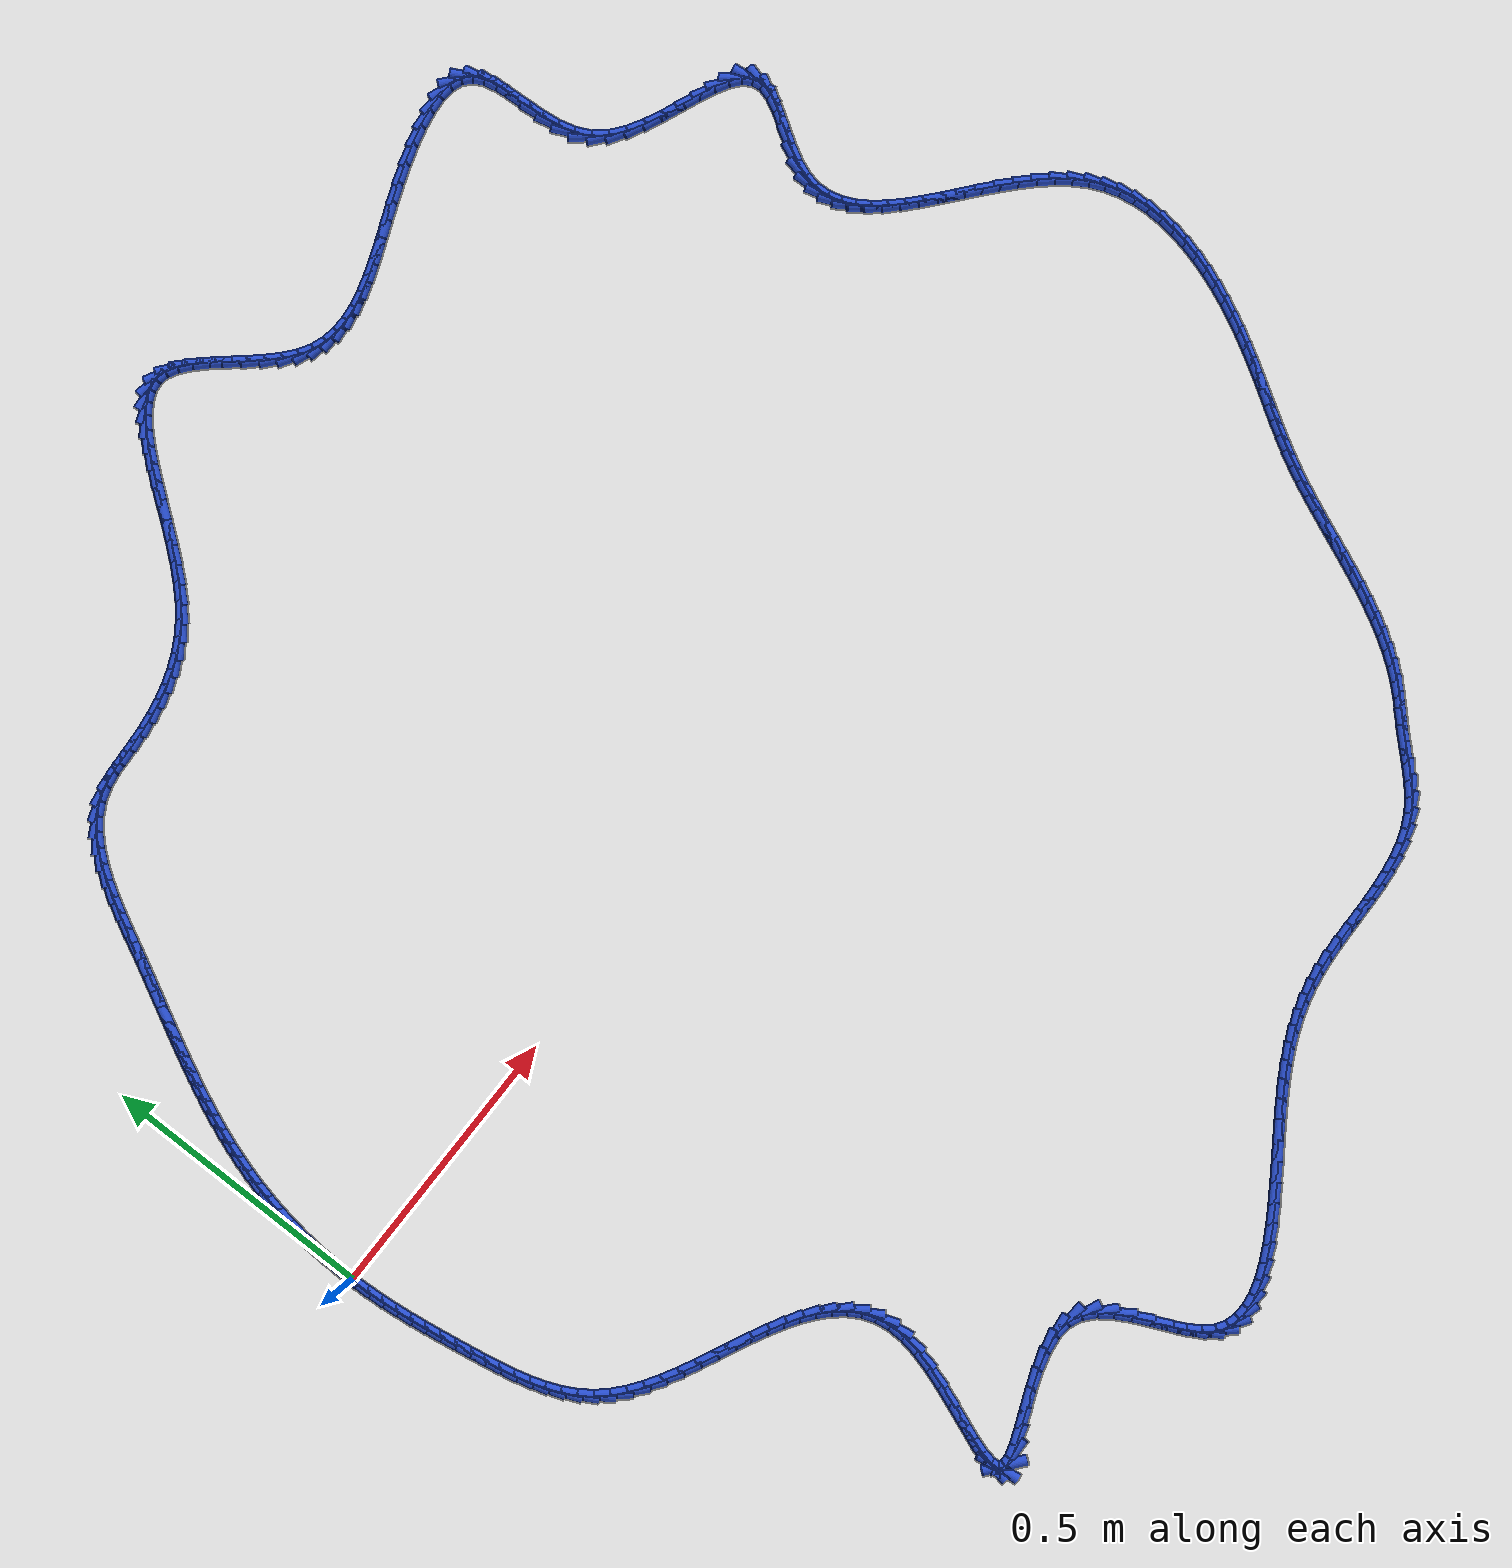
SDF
<sdf version="1.6">
 <world name="default">
  <light name="sun" type="directional">
   <pose>0 0 10 0 -0 0</pose>
   <diffuse>0.8 0.8 0.8 1</diffuse>
   <specular>0.2 0.2 0.2 1</specular>
   <attenuation>
    <range>1000</range>
    <constant>0.9</constant>
    <linear>0.01</linear>
    <quadratic>0.001</quadratic>
   </attenuation>
   <direction>-0.5 0.1 -0.9</direction>
  </light>
  <model name="ground_plane">
   <static>1</static>
   <link name="link">
    <collision name="collision">
     <geometry><plane><normal>0 0 1</normal><size>100 100</size></plane></geometry>
     <surface><friction><ode><mu>100</mu><mu2>50</mu2></ode></friction></surface>
    </collision>
    <visual name="visual">
     <cast_shadows>0</cast_shadows>
     <geometry><plane><normal>0 0 1</normal><size>100 100</size></plane></geometry>
     <material>
      <script><uri>file://media/materials/scripts/gazebo.material</uri><name>Gazebo/WhiteGlow</name></script>
     </material>
    </visual>
   </link>
  </model>
  <gravity>0 0 -9.8</gravity>
  <magnetic_field>6e-06 2.3e-05 -4.2e-05</magnetic_field>
  <atmosphere type="adiabatic"/>
  <physics name="default_physics" default="0" type="ode">
   <max_step_size>0.001</max_step_size>
   <real_time_factor>1</real_time_factor>
   <real_time_update_rate>1000</real_time_update_rate>
  </physics>
  <scene><ambient>0.4 0.4 0.4 1</ambient><background>0.7 0.7 0.7 1</background><shadows>1</shadows></scene>
  <spherical_coordinates>
   <surface_model>EARTH_WGS84</surface_model>
   <latitude_deg>0</latitude_deg>
   <longitude_deg>0</longitude_deg>
   <elevation>0</elevation>
   <heading_deg>0</heading_deg>
  </spherical_coordinates>
  <model name="line">
   <link name="link_0">
    <pose>1.214306433183765e-17 -2.7755575615628914e-17 0.01 0 1.57 -1.569403293261762</pose>
    <collision name="collision">
     <geometry><cylinder><radius>0.01</radius><length>0.08</length></cylinder></geometry>
    </collision>
    <visual name="visual">
     <material>
      <script><name>Gazebo/Blue</name><uri>file://media/materials/scripts/gazebo.material</uri></script>
     </material>
     <geometry><cylinder><radius>0.01</radius><length>0.08</length></cylinder></geometry>
    </visual>
   </link>
   <link name="link_1">
    <pose>-3.949599730603932e-05 0.028352491751786908 0.01 0 1.57 1.5391424583876925</pose>
    <collision name="collision">
     <geometry><cylinder><radius>0.01</radius><length>0.08</length></cylinder></geometry>
    </collision>
    <visual name="visual">
     <material>
      <script><name>Gazebo/Blue</name><uri>file://media/materials/scripts/gazebo.material</uri></script>
     </material>
     <geometry><cylinder><radius>0.01</radius><length>0.08</length></cylinder></geometry>
    </visual>
   </link>
   <link name="link_2">
    <pose>0.0008617968186554742 0.056816367391230284 0.01 0 1.57 1.5065247086572837</pose>
    <collision name="collision">
     <geometry><cylinder><radius>0.01</radius><length>0.08</length></cylinder></geometry>
    </collision>
    <visual name="visual">
     <material>
      <script><name>Gazebo/Blue</name><uri>file://media/materials/scripts/gazebo.material</uri></script>
     </material>
     <geometry><cylinder><radius>0.01</radius><length>0.08</length></cylinder></geometry>
    </visual>
   </link>
   <link name="link_3">
    <pose>0.002695351151080766 0.08530528649512793 0.01 0 1.57 1.4741054942030591</pose>
    <collision name="collision">
     <geometry><cylinder><radius>0.01</radius><length>0.08</length></cylinder></geometry>
    </collision>
    <visual name="visual">
     <material>
      <script><name>Gazebo/Blue</name><uri>file://media/materials/scripts/gazebo.material</uri></script>
     </material>
     <geometry><cylinder><radius>0.01</radius><length>0.08</length></cylinder></geometry>
    </visual>
   </link>
   <link name="link_4">
    <pose>0.005452639703166053 0.1137329086402777 0.01 0 1.57 1.4416570284435628</pose>
    <collision name="collision">
     <geometry><cylinder><radius>0.01</radius><length>0.08</length></cylinder></geometry>
    </collision>
    <visual name="visual">
     <material>
      <script><name>Gazebo/Blue</name><uri>file://media/materials/scripts/gazebo.material</uri></script>
     </material>
     <geometry><cylinder><radius>0.01</radius><length>0.08</length></cylinder></geometry>
    </visual>
   </link>
   <link name="link_5">
    <pose>0.009125135178107547 0.14201289340347745 0.01 0 1.57 1.4089507274478563</pose>
    <collision name="collision">
     <geometry><cylinder><radius>0.01</radius><length>0.08</length></cylinder></geometry>
    </collision>
    <visual name="visual">
     <material>
      <script><name>Gazebo/Blue</name><uri>file://media/materials/scripts/gazebo.material</uri></script>
     </material>
     <geometry><cylinder><radius>0.01</radius><length>0.08</length></cylinder></geometry>
    </visual>
   </link>
   <link name="link_6">
    <pose>0.013704310279101475 0.17005890036152504 0.01 0 1.57 1.37575355927471</pose>
    <collision name="collision">
     <geometry><cylinder><radius>0.01</radius><length>0.08</length></cylinder></geometry>
    </collision>
    <visual name="visual">
     <material>
      <script><name>Gazebo/Blue</name><uri>file://media/materials/scripts/gazebo.material</uri></script>
     </material>
     <geometry><cylinder><radius>0.01</radius><length>0.08</length></cylinder></geometry>
    </visual>
   </link>
   <link name="link_7">
    <pose>0.01918163770934405 0.19778458909121838 0.01 0 1.57 1.341824347660938</pose>
    <collision name="collision">
     <geometry><cylinder><radius>0.01</radius><length>0.08</length></cylinder></geometry>
    </collision>
    <visual name="visual">
     <material>
      <script><name>Gazebo/Blue</name><uri>file://media/materials/scripts/gazebo.material</uri></script>
     </material>
     <geometry><cylinder><radius>0.01</radius><length>0.08</length></cylinder></geometry>
    </visual>
   </link>
   <link name="link_8">
    <pose>0.02554859017203147 0.22510361916935517 0.01 0 1.57 1.3071662377353224</pose>
    <collision name="collision">
     <geometry><cylinder><radius>0.01</radius><length>0.08</length></cylinder></geometry>
    </collision>
    <visual name="visual">
     <material>
      <script><name>Gazebo/Blue</name><uri>file://media/materials/scripts/gazebo.material</uri></script>
     </material>
     <geometry><cylinder><radius>0.01</radius><length>0.08</length></cylinder></geometry>
    </visual>
   </link>
   <link name="link_9">
    <pose>0.03279278655953867 0.25194269415838494 0.01 0 1.57 1.273605408722673</pose>
    <collision name="collision">
     <geometry><cylinder><radius>0.01</radius><length>0.08</length></cylinder></geometry>
    </collision>
    <visual name="visual">
     <material>
      <script><name>Gazebo/Blue</name><uri>file://media/materials/scripts/gazebo.material</uri></script>
     </material>
     <geometry><cylinder><radius>0.01</radius><length>0.08</length></cylinder></geometry>
    </visual>
   </link>
   <link name="link_10">
    <pose>0.04087300568513552 0.2783261325778687 0.01 0 1.57 1.2422582898592898</pose>
    <collision name="collision">
     <geometry><cylinder><radius>0.01</radius><length>0.08</length></cylinder></geometry>
    </collision>
    <visual name="visual">
     <material>
      <script><name>Gazebo/Blue</name><uri>file://media/materials/scripts/gazebo.material</uri></script>
     </material>
     <geometry><cylinder><radius>0.01</radius><length>0.08</length></cylinder></geometry>
    </visual>
   </link>
   <link name="link_11">
    <pose>0.04973495872216867 0.3043224829616471 0.01 0 1.57 1.2133895899583158</pose>
    <collision name="collision">
     <geometry><cylinder><radius>0.01</radius><length>0.08</length></cylinder></geometry>
    </collision>
    <visual name="visual">
     <material>
      <script><name>Gazebo/Blue</name><uri>file://media/materials/scripts/gazebo.material</uri></script>
     </material>
     <geometry><cylinder><radius>0.01</radius><length>0.08</length></cylinder></geometry>
    </visual>
   </link>
   <link name="link_12">
    <pose>0.05932429211186404 0.3300005129422387 0.01 0 1.57 1.1872097440048386</pose>
    <collision name="collision">
     <geometry><cylinder><radius>0.01</radius><length>0.08</length></cylinder></geometry>
    </collision>
    <visual name="visual">
     <material>
      <script><name>Gazebo/Blue</name><uri>file://media/materials/scripts/gazebo.material</uri></script>
     </material>
     <geometry><cylinder><radius>0.01</radius><length>0.08</length></cylinder></geometry>
    </visual>
   </link>
   <link name="link_13">
    <pose>0.06958665229544758 0.3554289901521617 0.01 0 1.57 1.1638787342023296</pose>
    <collision name="collision">
     <geometry><cylinder><radius>0.01</radius><length>0.08</length></cylinder></geometry>
    </collision>
    <visual name="visual">
     <material>
      <script><name>Gazebo/Blue</name><uri>file://media/materials/scripts/gazebo.material</uri></script>
     </material>
     <geometry><cylinder><radius>0.01</radius><length>0.08</length></cylinder></geometry>
    </visual>
   </link>
   <link name="link_14">
    <pose>0.08046768571414523 0.3806766822239342 0.01 0 1.57 1.1435080649976357</pose>
    <collision name="collision">
     <geometry><cylinder><radius>0.01</radius><length>0.08</length></cylinder></geometry>
    </collision>
    <visual name="visual">
     <material>
      <script><name>Gazebo/Blue</name><uri>file://media/materials/scripts/gazebo.material</uri></script>
     </material>
     <geometry><cylinder><radius>0.01</radius><length>0.08</length></cylinder></geometry>
    </visual>
   </link>
   <link name="link_15">
    <pose>0.09191303880918288 0.4058123567900747 0.01 0 1.57 1.1261644985109405</pose>
    <collision name="collision">
     <geometry><cylinder><radius>0.01</radius><length>0.08</length></cylinder></geometry>
    </collision>
    <visual name="visual">
     <material>
      <script><name>Gazebo/Blue</name><uri>file://media/materials/scripts/gazebo.material</uri></script>
     </material>
     <geometry><cylinder><radius>0.01</radius><length>0.08</length></cylinder></geometry>
    </visual>
   </link>
   <link name="link_16">
    <pose>0.10386835802178647 0.4309047814831012 0.01 0 1.57 1.1118748430932415</pose>
    <collision name="collision">
     <geometry><cylinder><radius>0.01</radius><length>0.08</length></cylinder></geometry>
    </collision>
    <visual name="visual">
     <material>
      <script><name>Gazebo/Blue</name><uri>file://media/materials/scripts/gazebo.material</uri></script>
     </material>
     <geometry><cylinder><radius>0.01</radius><length>0.08</length></cylinder></geometry>
    </visual>
   </link>
   <link name="link_17">
    <pose>0.11627928979318203 0.4560227239355324 0.01 0 1.57 1.1006311700484854</pose>
    <collision name="collision">
     <geometry><cylinder><radius>0.01</radius><length>0.08</length></cylinder></geometry>
    </collision>
    <visual name="visual">
     <material>
      <script><name>Gazebo/Blue</name><uri>file://media/materials/scripts/gazebo.material</uri></script>
     </material>
     <geometry><cylinder><radius>0.01</radius><length>0.08</length></cylinder></geometry>
    </visual>
   </link>
   <link name="link_18">
    <pose>0.12909148056459532 0.4812349517798862 0.01 0 1.57 1.092395968686328</pose>
    <collision name="collision">
     <geometry><cylinder><radius>0.01</radius><length>0.08</length></cylinder></geometry>
    </collision>
    <visual name="visual">
     <material>
      <script><name>Gazebo/Blue</name><uri>file://media/materials/scripts/gazebo.material</uri></script>
     </material>
     <geometry><cylinder><radius>0.01</radius><length>0.08</length></cylinder></geometry>
    </visual>
   </link>
   <link name="link_19">
    <pose>0.14225057677725245 0.5066102326486811 0.01 0 1.57 1.0871069014804415</pose>
    <collision name="collision">
     <geometry><cylinder><radius>0.01</radius><length>0.08</length></cylinder></geometry>
    </collision>
    <visual name="visual">
     <material>
      <script><name>Gazebo/Blue</name><uri>file://media/materials/scripts/gazebo.material</uri></script>
     </material>
     <geometry><cylinder><radius>0.01</radius><length>0.08</length></cylinder></geometry>
    </visual>
   </link>
   <link name="link_20">
    <pose>0.15570222487237922 0.5322173341744353 0.01 0 1.57 1.0846809634818508</pose>
    <collision name="collision">
     <geometry><cylinder><radius>0.01</radius><length>0.08</length></cylinder></geometry>
    </collision>
    <visual name="visual">
     <material>
      <script><name>Gazebo/Blue</name><uri>file://media/materials/scripts/gazebo.material</uri></script>
     </material>
     <geometry><cylinder><radius>0.01</radius><length>0.08</length></cylinder></geometry>
    </visual>
   </link>
   <link name="link_21">
    <pose>0.16939207129120165 0.5581250239896671 0.01 0 1.57 1.0850179688617407</pose>
    <collision name="collision">
     <geometry><cylinder><radius>0.01</radius><length>0.08</length></cylinder></geometry>
    </collision>
    <visual name="visual">
     <material>
      <script><name>Gazebo/Blue</name><uri>file://media/materials/scripts/gazebo.material</uri></script>
     </material>
     <geometry><cylinder><radius>0.01</radius><length>0.08</length></cylinder></geometry>
    </visual>
   </link>
   <link name="link_22">
    <pose>0.1832657624749457 0.584402069726895 0.01 0 1.57 1.0880033772344389</pose>
    <collision name="collision">
     <geometry><cylinder><radius>0.01</radius><length>0.08</length></cylinder></geometry>
    </collision>
    <visual name="visual">
     <material>
      <script><name>Gazebo/Blue</name><uri>file://media/materials/scripts/gazebo.material</uri></script>
     </material>
     <geometry><cylinder><radius>0.01</radius><length>0.08</length></cylinder></geometry>
    </visual>
   </link>
   <link name="link_23">
    <pose>0.19726894486483715 0.6111172390186367 0.01 0 1.57 1.0934970126998422</pose>
    <collision name="collision">
     <geometry><cylinder><radius>0.01</radius><length>0.08</length></cylinder></geometry>
    </collision>
    <visual name="visual">
     <material>
      <script><name>Gazebo/Blue</name><uri>file://media/materials/scripts/gazebo.material</uri></script>
     </material>
     <geometry><cylinder><radius>0.01</radius><length>0.08</length></cylinder></geometry>
    </visual>
   </link>
   <link name="link_24">
    <pose>0.21134749198215816 0.638338836520691 0.01 0 1.57 1.0968751258752913</pose>
    <collision name="collision">
     <geometry><cylinder><radius>0.01</radius><length>0.08</length></cylinder></geometry>
    </collision>
    <visual name="visual">
     <material>
      <script><name>Gazebo/Blue</name><uri>file://media/materials/scripts/gazebo.material</uri></script>
     </material>
     <geometry><cylinder><radius>0.01</radius><length>0.08</length></cylinder></geometry>
    </visual>
   </link>
   <link name="link_25">
    <pose>0.22552411821669302 0.6659785017290284 0.01 0 1.57 1.0872540606396397</pose>
    <collision name="collision">
     <geometry><cylinder><radius>0.01</radius><length>0.08</length></cylinder></geometry>
    </collision>
    <visual name="visual">
     <material>
      <script><name>Gazebo/Blue</name><uri>file://media/materials/scripts/gazebo.material</uri></script>
     </material>
     <geometry><cylinder><radius>0.01</radius><length>0.08</length></cylinder></geometry>
    </visual>
   </link>
   <link name="link_26">
    <pose>0.24000983792865996 0.6935639632659113 0.01 0 1.57 1.062751894119248</pose>
    <collision name="collision">
     <geometry><cylinder><radius>0.01</radius><length>0.08</length></cylinder></geometry>
    </collision>
    <visual name="visual">
     <material>
      <script><name>Gazebo/Blue</name><uri>file://media/materials/scripts/gazebo.material</uri></script>
     </material>
     <geometry><cylinder><radius>0.01</radius><length>0.08</length></cylinder></geometry>
    </visual>
   </link>
   <link name="link_27">
    <pose>0.25504397944585805 0.7205652225006063 0.01 0 1.57 1.0221900369419215</pose>
    <collision name="collision">
     <geometry><cylinder><radius>0.01</radius><length>0.08</length></cylinder></geometry>
    </collision>
    <visual name="visual">
     <material>
      <script><name>Gazebo/Blue</name><uri>file://media/materials/scripts/gazebo.material</uri></script>
     </material>
     <geometry><cylinder><radius>0.01</radius><length>0.08</length></cylinder></geometry>
    </visual>
   </link>
   <link name="link_28">
    <pose>0.27086587109608634 0.7464522808023796 0.01 0 1.57 0.9634288575000315</pose>
    <collision name="collision">
     <geometry><cylinder><radius>0.01</radius><length>0.08</length></cylinder></geometry>
    </collision>
    <visual name="visual">
     <material>
      <script><name>Gazebo/Blue</name><uri>file://media/materials/scripts/gazebo.material</uri></script>
     </material>
     <geometry><cylinder><radius>0.01</radius><length>0.08</length></cylinder></geometry>
    </visual>
   </link>
   <link name="link_29">
    <pose>0.2877148412071439 0.7706951395404976 0.01 0 1.57 0.8834620583202922</pose>
    <collision name="collision">
     <geometry><cylinder><radius>0.01</radius><length>0.08</length></cylinder></geometry>
    </collision>
    <visual name="visual">
     <material>
      <script><name>Gazebo/Blue</name><uri>file://media/materials/scripts/gazebo.material</uri></script>
     </material>
     <geometry><cylinder><radius>0.01</radius><length>0.08</length></cylinder></geometry>
    </visual>
   </link>
   <link name="link_30">
    <pose>0.3058302181068301 0.7927638000842276 0.01 0 1.57 0.7788150981169186</pose>
    <collision name="collision">
     <geometry><cylinder><radius>0.01</radius><length>0.08</length></cylinder></geometry>
    </collision>
    <visual name="visual">
     <material>
      <script><name>Gazebo/Blue</name><uri>file://media/materials/scripts/gazebo.material</uri></script>
     </material>
     <geometry><cylinder><radius>0.01</radius><length>0.08</length></cylinder></geometry>
    </visual>
   </link>
   <link name="link_31">
    <pose>0.32545133012294375 0.8121282638028356 0.01 0 1.57 0.6466578356032517</pose>
    <collision name="collision">
     <geometry><cylinder><radius>0.01</radius><length>0.08</length></cylinder></geometry>
    </collision>
    <visual name="visual">
     <material>
      <script><name>Gazebo/Blue</name><uri>file://media/materials/scripts/gazebo.material</uri></script>
     </material>
     <geometry><cylinder><radius>0.01</radius><length>0.08</length></cylinder></geometry>
    </visual>
   </link>
   <link name="link_32">
    <pose>0.34681750558328417 0.8282585320655882 0.01 0 1.57 0.4870333298438299</pose>
    <collision name="collision">
     <geometry><cylinder><radius>0.01</radius><length>0.08</length></cylinder></geometry>
    </collision>
    <visual name="visual">
     <material>
      <script><name>Gazebo/Blue</name><uri>file://media/materials/scripts/gazebo.material</uri></script>
     </material>
     <geometry><cylinder><radius>0.01</radius><length>0.08</length></cylinder></geometry>
    </visual>
   </link>
   <link name="link_33">
    <pose>0.37016807281565056 0.8406246062417523 0.01 0 1.57 0.30742820067817783</pose>
    <collision name="collision">
     <geometry><cylinder><radius>0.01</radius><length>0.08</length></cylinder></geometry>
    </collision>
    <visual name="visual">
     <material>
      <script><name>Gazebo/Blue</name><uri>file://media/materials/scripts/gazebo.material</uri></script>
     </material>
     <geometry><cylinder><radius>0.01</radius><length>0.08</length></cylinder></geometry>
    </visual>
   </link>
   <link name="link_34">
    <pose>0.3957222099236863 0.8487378950800001 0.01 0 1.57 0.15746452261961666</pose>
    <collision name="collision">
     <geometry><cylinder><radius>0.01</radius><length>0.08</length></cylinder></geometry>
    </collision>
    <visual name="visual">
     <material>
      <script><name>Gazebo/Blue</name><uri>file://media/materials/scripts/gazebo.material</uri></script>
     </material>
     <geometry><cylinder><radius>0.01</radius><length>0.08</length></cylinder></geometry>
    </visual>
   </link>
   <link name="link_35">
    <pose>0.42321564034355014 0.8531032747310413 0.01 0 1.57 0.07446712019785998</pose>
    <collision name="collision">
     <geometry><cylinder><radius>0.01</radius><length>0.08</length></cylinder></geometry>
    </collision>
    <visual name="visual">
     <material>
      <script><name>Gazebo/Blue</name><uri>file://media/materials/scripts/gazebo.material</uri></script>
     </material>
     <geometry><cylinder><radius>0.01</radius><length>0.08</length></cylinder></geometry>
    </visual>
   </link>
   <link name="link_36">
    <pose>0.4518892538551447 0.8552424718177919 0.01 0 1.57 0.050892062239397115</pose>
    <collision name="collision">
     <geometry><cylinder><radius>0.01</radius><length>0.08</length></cylinder></geometry>
    </collision>
    <visual name="visual">
     <material>
      <script><name>Gazebo/Blue</name><uri>file://media/materials/scripts/gazebo.material</uri></script>
     </material>
     <geometry><cylinder><radius>0.01</radius><length>0.08</length></cylinder></geometry>
    </visual>
   </link>
   <link name="link_37">
    <pose>0.48096151383033836 0.8567232977500642 0.01 0 1.57 0.07739948501117896</pose>
    <collision name="collision">
     <geometry><cylinder><radius>0.01</radius><length>0.08</length></cylinder></geometry>
    </collision>
    <visual name="visual">
     <material>
      <script><name>Gazebo/Blue</name><uri>file://media/materials/scripts/gazebo.material</uri></script>
     </material>
     <geometry><cylinder><radius>0.01</radius><length>0.08</length></cylinder></geometry>
    </visual>
   </link>
   <link name="link_38">
    <pose>0.5097420762956917 0.8589553574296377 0.01 0 1.57 0.12423607483211829</pose>
    <collision name="collision">
     <geometry><cylinder><radius>0.01</radius><length>0.08</length></cylinder></geometry>
    </collision>
    <visual name="visual">
     <material>
      <script><name>Gazebo/Blue</name><uri>file://media/materials/scripts/gazebo.material</uri></script>
     </material>
     <geometry><cylinder><radius>0.01</radius><length>0.08</length></cylinder></geometry>
    </visual>
   </link>
   <link name="link_39">
    <pose>0.5380360648602363 0.8624886887642992 0.01 0 1.57 0.1813582369269799</pose>
    <collision name="collision">
     <geometry><cylinder><radius>0.01</radius><length>0.08</length></cylinder></geometry>
    </collision>
    <visual name="visual">
     <material>
      <script><name>Gazebo/Blue</name><uri>file://media/materials/scripts/gazebo.material</uri></script>
     </material>
     <geometry><cylinder><radius>0.01</radius><length>0.08</length></cylinder></geometry>
    </visual>
   </link>
   <link name="link_40">
    <pose>0.565816072054605 0.8675827944934003 0.01 0 1.57 0.24858504470689932</pose>
    <collision name="collision">
     <geometry><cylinder><radius>0.01</radius><length>0.08</length></cylinder></geometry>
    </collision>
    <visual name="visual">
     <material>
      <script><name>Gazebo/Blue</name><uri>file://media/materials/scripts/gazebo.material</uri></script>
     </material>
     <geometry><cylinder><radius>0.01</radius><length>0.08</length></cylinder></geometry>
    </visual>
   </link>
   <link name="link_41">
    <pose>0.5930548217666788 0.8744969494698323 0.01 0 1.57 0.3252360091168759</pose>
    <collision name="collision">
     <geometry><cylinder><radius>0.01</radius><length>0.08</length></cylinder></geometry>
    </collision>
    <visual name="visual">
     <material>
      <script><name>Gazebo/Blue</name><uri>file://media/materials/scripts/gazebo.material</uri></script>
     </material>
     <geometry><cylinder><radius>0.01</radius><length>0.08</length></cylinder></geometry>
    </visual>
   </link>
   <link name="link_42">
    <pose>0.6197250378843372 0.8834904285464852 0.01 0 1.57 0.4099783017791297</pose>
    <collision name="collision">
     <geometry><cylinder><radius>0.01</radius><length>0.08</length></cylinder></geometry>
    </collision>
    <visual name="visual">
     <material>
      <script><name>Gazebo/Blue</name><uri>file://media/materials/scripts/gazebo.material</uri></script>
     </material>
     <geometry><cylinder><radius>0.01</radius><length>0.08</length></cylinder></geometry>
    </visual>
   </link>
   <link name="link_43">
    <pose>0.6457994442954605 0.8948225065762505 0.01 0 1.57 0.5007813374077364</pose>
    <collision name="collision">
     <geometry><cylinder><radius>0.01</radius><length>0.08</length></cylinder></geometry>
    </collision>
    <visual name="visual">
     <material>
      <script><name>Gazebo/Blue</name><uri>file://media/materials/scripts/gazebo.material</uri></script>
     </material>
     <geometry><cylinder><radius>0.01</radius><length>0.08</length></cylinder></geometry>
    </visual>
   </link>
   <link name="link_44">
    <pose>0.6712507648879287 0.9087524584120191 0.01 0 1.57 0.5950353151412616</pose>
    <collision name="collision">
     <geometry><cylinder><radius>0.01</radius><length>0.08</length></cylinder></geometry>
    </collision>
    <visual name="visual">
     <material>
      <script><name>Gazebo/Blue</name><uri>file://media/materials/scripts/gazebo.material</uri></script>
     </material>
     <geometry><cylinder><radius>0.01</radius><length>0.08</length></cylinder></geometry>
    </visual>
   </link>
   <link name="link_45">
    <pose>0.6960517235496214 0.9255395589066813 0.01 0 1.57 0.6896536188897094</pose>
    <collision name="collision">
     <geometry><cylinder><radius>0.01</radius><length>0.08</length></cylinder></geometry>
    </collision>
    <visual name="visual">
     <material>
      <script><name>Gazebo/Blue</name><uri>file://media/materials/scripts/gazebo.material</uri></script>
     </material>
     <geometry><cylinder><radius>0.01</radius><length>0.08</length></cylinder></geometry>
    </visual>
   </link>
   <link name="link_46">
    <pose>0.7201756261140797 0.9454358426621609 0.01 0 1.57 0.7730505174797482</pose>
    <collision name="collision">
     <geometry><cylinder><radius>0.01</radius><length>0.08</length></cylinder></geometry>
    </collision>
    <visual name="visual">
     <material>
      <script><name>Gazebo/Blue</name><uri>file://media/materials/scripts/gazebo.material</uri></script>
     </material>
     <geometry><cylinder><radius>0.01</radius><length>0.08</length></cylinder></geometry>
    </visual>
   </link>
   <link name="link_47">
    <pose>0.743626238971905 0.9683143706190532 0.01 0 1.57 0.8343226368081349</pose>
    <collision name="collision">
     <geometry><cylinder><radius>0.01</radius><length>0.08</length></cylinder></geometry>
    </collision>
    <visual name="visual">
     <material>
      <script><name>Gazebo/Blue</name><uri>file://media/materials/scripts/gazebo.material</uri></script>
     </material>
     <geometry><cylinder><radius>0.01</radius><length>0.08</length></cylinder></geometry>
    </visual>
   </link>
   <link name="link_48">
    <pose>0.7664521441412894 0.9934906320872209 0.01 0 1.57 0.8768088855084678</pose>
    <collision name="collision">
     <geometry><cylinder><radius>0.01</radius><length>0.08</length></cylinder></geometry>
    </collision>
    <visual name="visual">
     <material>
      <script><name>Gazebo/Blue</name><uri>file://media/materials/scripts/gazebo.material</uri></script>
     </material>
     <geometry><cylinder><radius>0.01</radius><length>0.08</length></cylinder></geometry>
    </visual>
   </link>
   <link name="link_49">
    <pose>0.7887055114629061 1.0202354786432424 0.01 0 1.57 0.903491809310568</pose>
    <collision name="collision">
     <geometry><cylinder><radius>0.01</radius><length>0.08</length></cylinder></geometry>
    </collision>
    <visual name="visual">
     <material>
      <script><name>Gazebo/Blue</name><uri>file://media/materials/scripts/gazebo.material</uri></script>
     </material>
     <geometry><cylinder><radius>0.01</radius><length>0.08</length></cylinder></geometry>
    </visual>
   </link>
   <link name="link_50">
    <pose>0.810438510777429 1.0478197618636964 0.01 0 1.57 0.915979554030327</pose>
    <collision name="collision">
     <geometry><cylinder><radius>0.01</radius><length>0.08</length></cylinder></geometry>
    </collision>
    <visual name="visual">
     <material>
      <script><name>Gazebo/Blue</name><uri>file://media/materials/scripts/gazebo.material</uri></script>
     </material>
     <geometry><cylinder><radius>0.01</radius><length>0.08</length></cylinder></geometry>
    </visual>
   </link>
   <link name="link_51">
    <pose>0.8317033119255306 1.075514333325161 0.01 0 1.57 0.914606592212624</pose>
    <collision name="collision">
     <geometry><cylinder><radius>0.01</radius><length>0.08</length></cylinder></geometry>
    </collision>
    <visual name="visual">
     <material>
      <script><name>Gazebo/Blue</name><uri>file://media/materials/scripts/gazebo.material</uri></script>
     </material>
     <geometry><cylinder><radius>0.01</radius><length>0.08</length></cylinder></geometry>
    </visual>
   </link>
   <link name="link_52">
    <pose>0.852552084747885 1.1025900446042158 0.01 0 1.57 0.8983644470001207</pose>
    <collision name="collision">
     <geometry><cylinder><radius>0.01</radius><length>0.08</length></cylinder></geometry>
    </collision>
    <visual name="visual">
     <material>
      <script><name>Gazebo/Blue</name><uri>file://media/materials/scripts/gazebo.material</uri></script>
     </material>
     <geometry><cylinder><radius>0.01</radius><length>0.08</length></cylinder></geometry>
    </visual>
   </link>
   <link name="link_53">
    <pose>0.8730369990851651 1.1283177472774386 0.01 0 1.57 0.8645800655813473</pose>
    <collision name="collision">
     <geometry><cylinder><radius>0.01</radius><length>0.08</length></cylinder></geometry>
    </collision>
    <visual name="visual">
     <material>
      <script><name>Gazebo/Blue</name><uri>file://media/materials/scripts/gazebo.material</uri></script>
     </material>
     <geometry><cylinder><radius>0.01</radius><length>0.08</length></cylinder></geometry>
    </visual>
   </link>
   <link name="link_54">
    <pose>0.8932102247780446 1.1519682929214088 0.01 0 1.57 0.8082249184652066</pose>
    <collision name="collision">
     <geometry><cylinder><radius>0.01</radius><length>0.08</length></cylinder></geometry>
    </collision>
    <visual name="visual">
     <material>
      <script><name>Gazebo/Blue</name><uri>file://media/materials/scripts/gazebo.material</uri></script>
     </material>
     <geometry><cylinder><radius>0.01</radius><length>0.08</length></cylinder></geometry>
    </visual>
   </link>
   <link name="link_55">
    <pose>0.9131239316671964 1.1728125331127044 0.01 0 1.57 0.720715799810971</pose>
    <collision name="collision">
     <geometry><cylinder><radius>0.01</radius><length>0.08</length></cylinder></geometry>
    </collision>
    <visual name="visual">
     <material>
      <script><name>Gazebo/Blue</name><uri>file://media/materials/scripts/gazebo.material</uri></script>
     </material>
     <geometry><cylinder><radius>0.01</radius><length>0.08</length></cylinder></geometry>
    </visual>
   </link>
   <link name="link_56">
    <pose>0.9328302895932938 1.190121319427904 0.01 0 1.57 0.588358914141903</pose>
    <collision name="collision">
     <geometry><cylinder><radius>0.01</radius><length>0.08</length></cylinder></geometry>
    </collision>
    <visual name="visual">
     <material>
      <script><name>Gazebo/Blue</name><uri>file://media/materials/scripts/gazebo.material</uri></script>
     </material>
     <geometry><cylinder><radius>0.01</radius><length>0.08</length></cylinder></geometry>
    </visual>
   </link>
   <link name="link_57">
    <pose>0.9523814683970105 1.2031655034435866 0.01 0 1.57 0.3924681050909312</pose>
    <collision name="collision">
     <geometry><cylinder><radius>0.01</radius><length>0.08</length></cylinder></geometry>
    </collision>
    <visual name="visual">
     <material>
      <script><name>Gazebo/Blue</name><uri>file://media/materials/scripts/gazebo.material</uri></script>
     </material>
     <geometry><cylinder><radius>0.01</radius><length>0.08</length></cylinder></geometry>
    </visual>
   </link>
   <link name="link_58">
    <pose>0.9718296379190196 1.211215936736331 0.01 0 1.57 0.11942153332450568</pose>
    <collision name="collision">
     <geometry><cylinder><radius>0.01</radius><length>0.08</length></cylinder></geometry>
    </collision>
    <visual name="visual">
     <material>
      <script><name>Gazebo/Blue</name><uri>file://media/materials/scripts/gazebo.material</uri></script>
     </material>
     <geometry><cylinder><radius>0.01</radius><length>0.08</length></cylinder></geometry>
    </visual>
   </link>
   <link name="link_59">
    <pose>0.9912269679999947 1.213543470882716 0.01 0 1.57 -0.20945573124398648</pose>
    <collision name="collision">
     <geometry><cylinder><radius>0.01</radius><length>0.08</length></cylinder></geometry>
    </collision>
    <visual name="visual">
     <material>
      <script><name>Gazebo/Blue</name><uri>file://media/materials/scripts/gazebo.material</uri></script>
     </material>
     <geometry><cylinder><radius>0.01</radius><length>0.08</length></cylinder></geometry>
    </visual>
   </link>
   <link name="link_60">
    <pose>1.0106256419870983 1.2094198265552434 0.01 0 1.57 -0.5058337807228935</pose>
    <collision name="collision">
     <geometry><cylinder><radius>0.01</radius><length>0.08</length></cylinder></geometry>
    </collision>
    <visual name="visual">
     <material>
      <script><name>Gazebo/Blue</name><uri>file://media/materials/scripts/gazebo.material</uri></script>
     </material>
     <geometry><cylinder><radius>0.01</radius><length>0.08</length></cylinder></geometry>
    </visual>
   </link>
   <link name="link_61">
    <pose>1.0300859864046774 1.1986407097453744 0.01 0 1.57 -0.6914553878536778</pose>
    <collision name="collision">
     <geometry><cylinder><radius>0.01</radius><length>0.08</length></cylinder></geometry>
    </collision>
    <visual name="visual">
     <material>
      <script><name>Gazebo/Blue</name><uri>file://media/materials/scripts/gazebo.material</uri></script>
     </material>
     <geometry><cylinder><radius>0.01</radius><length>0.08</length></cylinder></geometry>
    </visual>
   </link>
   <link name="link_62">
    <pose>1.04969025203477 1.1824125766834868 0.01 0 1.57 -0.7954201180225066</pose>
    <collision name="collision">
     <geometry><cylinder><radius>0.01</radius><length>0.08</length></cylinder></geometry>
    </collision>
    <visual name="visual">
     <material>
      <script><name>Gazebo/Blue</name><uri>file://media/materials/scripts/gazebo.material</uri></script>
     </material>
     <geometry><cylinder><radius>0.01</radius><length>0.08</length></cylinder></geometry>
    </visual>
   </link>
   <link name="link_63">
    <pose>1.0695243419502727 1.1621768958988958 0.01 0 1.57 -0.8470625001300783</pose>
    <collision name="collision">
     <geometry><cylinder><radius>0.01</radius><length>0.08</length></cylinder></geometry>
    </collision>
    <visual name="visual">
     <material>
      <script><name>Gazebo/Blue</name><uri>file://media/materials/scripts/gazebo.material</uri></script>
     </material>
     <geometry><cylinder><radius>0.01</radius><length>0.08</length></cylinder></geometry>
    </visual>
   </link>
   <link name="link_64">
    <pose>1.089674159224083 1.139375135920917 0.01 0 1.57 -0.8611318258141664</pose>
    <collision name="collision">
     <geometry><cylinder><radius>0.01</radius><length>0.08</length></cylinder></geometry>
    </collision>
    <visual name="visual">
     <material>
      <script><name>Gazebo/Blue</name><uri>file://media/materials/scripts/gazebo.material</uri></script>
     </material>
     <geometry><cylinder><radius>0.01</radius><length>0.08</length></cylinder></geometry>
    </visual>
   </link>
   <link name="link_65">
    <pose>1.110225606929098 1.1154487652788665 0.01 0 1.57 -0.8429073170418129</pose>
    <collision name="collision">
     <geometry><cylinder><radius>0.01</radius><length>0.08</length></cylinder></geometry>
    </collision>
    <visual name="visual">
     <material>
      <script><name>Gazebo/Blue</name><uri>file://media/materials/scripts/gazebo.material</uri></script>
     </material>
     <geometry><cylinder><radius>0.01</radius><length>0.08</length></cylinder></geometry>
    </visual>
   </link>
   <link name="link_66">
    <pose>1.1312645881382144 1.091839252502059 0.01 0 1.57 -0.7908916377381817</pose>
    <collision name="collision">
     <geometry><cylinder><radius>0.01</radius><length>0.08</length></cylinder></geometry>
    </collision>
    <visual name="visual">
     <material>
      <script><name>Gazebo/Blue</name><uri>file://media/materials/scripts/gazebo.material</uri></script>
     </material>
     <geometry><cylinder><radius>0.01</radius><length>0.08</length></cylinder></geometry>
    </visual>
   </link>
   <link name="link_67">
    <pose>1.1528770059243294 1.069988066119811 0.01 0 1.57 -0.697160447937442</pose>
    <collision name="collision">
     <geometry><cylinder><radius>0.01</radius><length>0.08</length></cylinder></geometry>
    </collision>
    <visual name="visual">
     <material>
      <script><name>Gazebo/Blue</name><uri>file://media/materials/scripts/gazebo.material</uri></script>
     </material>
     <geometry><cylinder><radius>0.01</radius><length>0.08</length></cylinder></geometry>
    </visual>
   </link>
   <link name="link_68">
    <pose>1.1751487633603401 1.0513366746614365 0.01 0 1.57 -0.548528466043791</pose>
    <collision name="collision">
     <geometry><cylinder><radius>0.01</radius><length>0.08</length></cylinder></geometry>
    </collision>
    <visual name="visual">
     <material>
      <script><name>Gazebo/Blue</name><uri>file://media/materials/scripts/gazebo.material</uri></script>
     </material>
     <geometry><cylinder><radius>0.01</radius><length>0.08</length></cylinder></geometry>
    </visual>
   </link>
   <link name="link_69">
    <pose>1.1981641821962783 1.0372723582895738 0.01 0 1.57 -0.36453807532582233</pose>
    <collision name="collision">
     <geometry><cylinder><radius>0.01</radius><length>0.08</length></cylinder></geometry>
    </collision>
    <visual name="visual">
     <material>
      <script><name>Gazebo/Blue</name><uri>file://media/materials/scripts/gazebo.material</uri></script>
     </material>
     <geometry><cylinder><radius>0.01</radius><length>0.08</length></cylinder></geometry>
    </visual>
   </link>
   <link name="link_70">
    <pose>1.2219784780293776 1.0281849949817896 0.01 0 1.57 -0.18440869892412518</pose>
    <collision name="collision">
     <geometry><cylinder><radius>0.01</radius><length>0.08</length></cylinder></geometry>
    </collision>
    <visual name="visual">
     <material>
      <script><name>Gazebo/Blue</name><uri>file://media/materials/scripts/gazebo.material</uri></script>
     </material>
     <geometry><cylinder><radius>0.01</radius><length>0.08</length></cylinder></geometry>
    </visual>
   </link>
   <link name="link_71">
    <pose>1.2466213018355772 1.0235884208245636 0.01 0 1.57 -0.02437688904333088</pose>
    <collision name="collision">
     <geometry><cylinder><radius>0.01</radius><length>0.08</length></cylinder></geometry>
    </collision>
    <visual name="visual">
     <material>
      <script><name>Gazebo/Blue</name><uri>file://media/materials/scripts/gazebo.material</uri></script>
     </material>
     <geometry><cylinder><radius>0.01</radius><length>0.08</length></cylinder></geometry>
    </visual>
   </link>
   <link name="link_72">
    <pose>1.2721214353138217 1.022966683743123 0.01 0 1.57 0.10711230518315785</pose>
    <collision name="collision">
     <geometry><cylinder><radius>0.01</radius><length>0.08</length></cylinder></geometry>
    </collision>
    <visual name="visual">
     <material>
      <script><name>Gazebo/Blue</name><uri>file://media/materials/scripts/gazebo.material</uri></script>
     </material>
     <geometry><cylinder><radius>0.01</radius><length>0.08</length></cylinder></geometry>
    </visual>
   </link>
   <link name="link_73">
    <pose>1.2985076601630554 1.0258038316626956 0.01 0 1.57 0.20863520247710268</pose>
    <collision name="collision">
     <geometry><cylinder><radius>0.01</radius><length>0.08</length></cylinder></geometry>
    </collision>
    <visual name="visual">
     <material>
      <script><name>Gazebo/Blue</name><uri>file://media/materials/scripts/gazebo.material</uri></script>
     </material>
     <geometry><cylinder><radius>0.01</radius><length>0.08</length></cylinder></geometry>
    </visual>
   </link>
   <link name="link_74">
    <pose>1.3258087580822235 1.0315839125085091 0.01 0 1.57 0.2827825981774086</pose>
    <collision name="collision">
     <geometry><cylinder><radius>0.01</radius><length>0.08</length></cylinder></geometry>
    </collision>
    <visual name="visual">
     <material>
      <script><name>Gazebo/Blue</name><uri>file://media/materials/scripts/gazebo.material</uri></script>
     </material>
     <geometry><cylinder><radius>0.01</radius><length>0.08</length></cylinder></geometry>
    </visual>
   </link>
   <link name="link_75">
    <pose>1.3540535107702707 1.039790974205791 0.01 0 1.57 0.33338024632950375</pose>
    <collision name="collision">
     <geometry><cylinder><radius>0.01</radius><length>0.08</length></cylinder></geometry>
    </collision>
    <visual name="visual">
     <material>
      <script><name>Gazebo/Blue</name><uri>file://media/materials/scripts/gazebo.material</uri></script>
     </material>
     <geometry><cylinder><radius>0.01</radius><length>0.08</length></cylinder></geometry>
    </visual>
   </link>
   <link name="link_76">
    <pose>1.3832706999261415 1.0499090646797686 0.01 0 1.57 0.3640192103134254</pose>
    <collision name="collision">
     <geometry><cylinder><radius>0.01</radius><length>0.08</length></cylinder></geometry>
    </collision>
    <visual name="visual">
     <material>
      <script><name>Gazebo/Blue</name><uri>file://media/materials/scripts/gazebo.material</uri></script>
     </material>
     <geometry><cylinder><radius>0.01</radius><length>0.08</length></cylinder></geometry>
    </visual>
   </link>
   <link name="link_77">
    <pose>1.4134891072487812 1.06142223185567 0.01 0 1.57 0.37754905623832963</pose>
    <collision name="collision">
     <geometry><cylinder><radius>0.01</radius><length>0.08</length></cylinder></geometry>
    </collision>
    <visual name="visual">
     <material>
      <script><name>Gazebo/Blue</name><uri>file://media/materials/scripts/gazebo.material</uri></script>
     </material>
     <geometry><cylinder><radius>0.01</radius><length>0.08</length></cylinder></geometry>
    </visual>
   </link>
   <link name="link_78">
    <pose>1.4447375144371337 1.073814523658723 0.01 0 1.57 0.3760312948506339</pose>
    <collision name="collision">
     <geometry><cylinder><radius>0.01</radius><length>0.08</length></cylinder></geometry>
    </collision>
    <visual name="visual">
     <material>
      <script><name>Gazebo/Blue</name><uri>file://media/materials/scripts/gazebo.material</uri></script>
     </material>
     <geometry><cylinder><radius>0.01</radius><length>0.08</length></cylinder></geometry>
    </visual>
   </link>
   <link name="link_79">
    <pose>1.4770447031901448 1.0865699880141548 0.01 0 1.57 0.36089655454381203</pose>
    <collision name="collision">
     <geometry><cylinder><radius>0.01</radius><length>0.08</length></cylinder></geometry>
    </collision>
    <visual name="visual">
     <material>
      <script><name>Gazebo/Blue</name><uri>file://media/materials/scripts/gazebo.material</uri></script>
     </material>
     <geometry><cylinder><radius>0.01</radius><length>0.08</length></cylinder></geometry>
    </visual>
   </link>
   <link name="link_80">
    <pose>1.5104307156463077 1.0991707630271332 0.01 0 1.57 0.3342164246351071</pose>
    <collision name="collision">
     <geometry><cylinder><radius>0.01</radius><length>0.08</length></cylinder></geometry>
    </collision>
    <visual name="visual">
     <material>
      <script><name>Gazebo/Blue</name><uri>file://media/materials/scripts/gazebo.material</uri></script>
     </material>
     <geometry><cylinder><radius>0.01</radius><length>0.08</length></cylinder></geometry>
    </visual>
   </link>
   <link name="link_81">
    <pose>1.5445550931049614 1.1110202080429676 0.01 0 1.57 0.29640694495373715</pose>
    <collision name="collision">
     <geometry><cylinder><radius>0.01</radius><length>0.08</length></cylinder></geometry>
    </collision>
    <visual name="visual">
     <material>
      <script><name>Gazebo/Blue</name><uri>file://media/materials/scripts/gazebo.material</uri></script>
     </material>
     <geometry><cylinder><radius>0.01</radius><length>0.08</length></cylinder></geometry>
    </visual>
   </link>
   <link name="link_82">
    <pose>1.5785967024421943 1.1214166426099732 0.01 0 1.57 0.24379468541604338</pose>
    <collision name="collision">
     <geometry><cylinder><radius>0.01</radius><length>0.08</length></cylinder></geometry>
    </collision>
    <visual name="visual">
     <material>
      <script><name>Gazebo/Blue</name><uri>file://media/materials/scripts/gazebo.material</uri></script>
     </material>
     <geometry><cylinder><radius>0.01</radius><length>0.08</length></cylinder></geometry>
    </visual>
   </link>
   <link name="link_83">
    <pose>1.6117010109179404 1.1296510875962578 0.01 0 1.57 0.1696424905337586</pose>
    <collision name="collision">
     <geometry><cylinder><radius>0.01</radius><length>0.08</length></cylinder></geometry>
    </collision>
    <visual name="visual">
     <material>
      <script><name>Gazebo/Blue</name><uri>file://media/materials/scripts/gazebo.material</uri></script>
     </material>
     <geometry><cylinder><radius>0.01</radius><length>0.08</length></cylinder></geometry>
    </visual>
   </link>
   <link name="link_84">
    <pose>1.6430134857921324 1.1350145638699265 0.01 0 1.57 0.0621372243248523</pose>
    <collision name="collision">
     <geometry><cylinder><radius>0.01</radius><length>0.08</length></cylinder></geometry>
    </collision>
    <visual name="visual">
     <material>
      <script><name>Gazebo/Blue</name><uri>file://media/materials/scripts/gazebo.material</uri></script>
     </material>
     <geometry><cylinder><radius>0.01</radius><length>0.08</length></cylinder></geometry>
    </visual>
   </link>
   <link name="link_85">
    <pose>1.6716795943247016 1.1367980922990857 0.01 0 1.57 -0.09923103418605521</pose>
    <collision name="collision">
     <geometry><cylinder><radius>0.01</radius><length>0.08</length></cylinder></geometry>
    </collision>
    <visual name="visual">
     <material>
      <script><name>Gazebo/Blue</name><uri>file://media/materials/scripts/gazebo.material</uri></script>
     </material>
     <geometry><cylinder><radius>0.01</radius><length>0.08</length></cylinder></geometry>
    </visual>
   </link>
   <link name="link_86">
    <pose>1.6968448037755817 1.1342926937518418 0.01 0 1.57 -0.3460568235937788</pose>
    <collision name="collision">
     <geometry><cylinder><radius>0.01</radius><length>0.08</length></cylinder></geometry>
    </collision>
    <visual name="visual">
     <material>
      <script><name>Gazebo/Blue</name><uri>file://media/materials/scripts/gazebo.material</uri></script>
     </material>
     <geometry><cylinder><radius>0.01</radius><length>0.08</length></cylinder></geometry>
    </visual>
   </link>
   <link name="link_87">
    <pose>1.7176545814047062 1.1267893890963014 0.01 0 1.57 -0.7026415769738923</pose>
    <collision name="collision">
     <geometry><cylinder><radius>0.01</radius><length>0.08</length></cylinder></geometry>
    </collision>
    <visual name="visual">
     <material>
      <script><name>Gazebo/Blue</name><uri>file://media/materials/scripts/gazebo.material</uri></script>
     </material>
     <geometry><cylinder><radius>0.01</radius><length>0.08</length></cylinder></geometry>
    </visual>
   </link>
   <link name="link_88">
    <pose>1.7332544233568012 1.1135792229174362 0.01 0 1.57 -1.0917864903423224</pose>
    <collision name="collision">
     <geometry><cylinder><radius>0.01</radius><length>0.08</length></cylinder></geometry>
    </collision>
    <visual name="visual">
     <material>
      <script><name>Gazebo/Blue</name><uri>file://media/materials/scripts/gazebo.material</uri></script>
     </material>
     <geometry><cylinder><radius>0.01</radius><length>0.08</length></cylinder></geometry>
    </visual>
   </link>
   <link name="link_89">
    <pose>1.7432507027102917 1.094331658848473 0.01 0 1.57 -1.3430122461683796</pose>
    <collision name="collision">
     <geometry><cylinder><radius>0.01</radius><length>0.08</length></cylinder></geometry>
    </collision>
    <visual name="visual">
     <material>
      <script><name>Gazebo/Blue</name><uri>file://media/materials/scripts/gazebo.material</uri></script>
     </material>
     <geometry><cylinder><radius>0.01</radius><length>0.08</length></cylinder></geometry>
    </visual>
   </link>
   <link name="link_90">
    <pose>1.7488785516576342 1.0700535098857828 0.01 0 1.57 -1.4692361141527863</pose>
    <collision name="collision">
     <geometry><cylinder><radius>0.01</radius><length>0.08</length></cylinder></geometry>
    </collision>
    <visual name="visual">
     <material>
      <script><name>Gazebo/Blue</name><uri>file://media/materials/scripts/gazebo.material</uri></script>
     </material>
     <geometry><cylinder><radius>0.01</radius><length>0.08</length></cylinder></geometry>
    </visual>
   </link>
   <link name="link_91">
    <pose>1.751732731340771 1.0420468748923941 0.01 0 1.57 -1.5158040078895092</pose>
    <collision name="collision">
     <geometry><cylinder><radius>0.01</radius><length>0.08</length></cylinder></geometry>
    </collision>
    <visual name="visual">
     <material>
      <script><name>Gazebo/Blue</name><uri>file://media/materials/scripts/gazebo.material</uri></script>
     </material>
     <geometry><cylinder><radius>0.01</radius><length>0.08</length></cylinder></geometry>
    </visual>
   </link>
   <link name="link_92">
    <pose>1.7534080029016428 1.0116138527313332 0.01 0 1.57 -1.5046287128860094</pose>
    <collision name="collision">
     <geometry><cylinder><radius>0.01</radius><length>0.08</length></cylinder></geometry>
    </collision>
    <visual name="visual">
     <material>
      <script><name>Gazebo/Blue</name><uri>file://media/materials/scripts/gazebo.material</uri></script>
     </material>
     <geometry><cylinder><radius>0.01</radius><length>0.08</length></cylinder></geometry>
    </visual>
   </link>
   <link name="link_93">
    <pose>1.7554991274821914 0.980056542265628 0.01 0 1.57 -1.4408192908810187</pose>
    <collision name="collision">
     <geometry><cylinder><radius>0.01</radius><length>0.08</length></cylinder></geometry>
    </collision>
    <visual name="visual">
     <material>
      <script><name>Gazebo/Blue</name><uri>file://media/materials/scripts/gazebo.material</uri></script>
     </material>
     <geometry><cylinder><radius>0.01</radius><length>0.08</length></cylinder></geometry>
    </visual>
   </link>
   <link name="link_94">
    <pose>1.7596008662243587 0.9486770423583066 0.01 0 1.57 -1.3185214401000014</pose>
    <collision name="collision">
     <geometry><cylinder><radius>0.01</radius><length>0.08</length></cylinder></geometry>
    </collision>
    <visual name="visual">
     <material>
      <script><name>Gazebo/Blue</name><uri>file://media/materials/scripts/gazebo.material</uri></script>
     </material>
     <geometry><cylinder><radius>0.01</radius><length>0.08</length></cylinder></geometry>
    </visual>
   </link>
   <link name="link_95">
    <pose>1.7673079802700853 0.9187774518723961 0.01 0 1.57 -1.1265540020992637</pose>
    <collision name="collision">
     <geometry><cylinder><radius>0.01</radius><length>0.08</length></cylinder></geometry>
    </collision>
    <visual name="visual">
     <material>
      <script><name>Gazebo/Blue</name><uri>file://media/materials/scripts/gazebo.material</uri></script>
     </material>
     <geometry><cylinder><radius>0.01</radius><length>0.08</length></cylinder></geometry>
    </visual>
   </link>
   <link name="link_96">
    <pose>1.7802152307613135 0.891659869670924 0.01 0 1.57 -0.880917438780095</pose>
    <collision name="collision">
     <geometry><cylinder><radius>0.01</radius><length>0.08</length></cylinder></geometry>
    </collision>
    <visual name="visual">
     <material>
      <script><name>Gazebo/Blue</name><uri>file://media/materials/scripts/gazebo.material</uri></script>
     </material>
     <geometry><cylinder><radius>0.01</radius><length>0.08</length></cylinder></geometry>
    </visual>
   </link>
   <link name="link_97">
    <pose>1.7994592034599086 0.8683375882702103 0.01 0 1.57 -0.6782252136252166</pose>
    <collision name="collision">
     <geometry><cylinder><radius>0.01</radius><length>0.08</length></cylinder></geometry>
    </collision>
    <visual name="visual">
     <material>
      <script><name>Gazebo/Blue</name><uri>file://media/materials/scripts/gazebo.material</uri></script>
     </material>
     <geometry><cylinder><radius>0.01</radius><length>0.08</length></cylinder></geometry>
    </visual>
   </link>
   <link name="link_98">
    <pose>1.8240782360928025 0.848501290164714 0.01 0 1.57 -0.539869519421529</pose>
    <collision name="collision">
     <geometry><cylinder><radius>0.01</radius><length>0.08</length></cylinder></geometry>
    </collision>
    <visual name="visual">
     <material>
      <script><name>Gazebo/Blue</name><uri>file://media/materials/scripts/gazebo.material</uri></script>
     </material>
     <geometry><cylinder><radius>0.01</radius><length>0.08</length></cylinder></geometry>
    </visual>
   </link>
   <link name="link_99">
    <pose>1.8525103719357185 0.8314632681428099 0.01 0 1.57 -0.4527917715765439</pose>
    <collision name="collision">
     <geometry><cylinder><radius>0.01</radius><length>0.08</length></cylinder></geometry>
    </collision>
    <visual name="visual">
     <material>
      <script><name>Gazebo/Blue</name><uri>file://media/materials/scripts/gazebo.material</uri></script>
     </material>
     <geometry><cylinder><radius>0.01</radius><length>0.08</length></cylinder></geometry>
    </visual>
   </link>
   <link name="link_100">
    <pose>1.8831936061579881 0.8165357846694805 0.01 0 1.57 -0.40649025239723474</pose>
    <collision name="collision">
     <geometry><cylinder><radius>0.01</radius><length>0.08</length></cylinder></geometry>
    </collision>
    <visual name="visual">
     <material>
      <script><name>Gazebo/Blue</name><uri>file://media/materials/scripts/gazebo.material</uri></script>
     </material>
     <geometry><cylinder><radius>0.01</radius><length>0.08</length></cylinder></geometry>
    </visual>
   </link>
   <link name="link_101">
    <pose>1.9145659339289427 0.8030311022097084 0.01 0 1.57 -0.3965088349581922</pose>
    <collision name="collision">
     <geometry><cylinder><radius>0.01</radius><length>0.08</length></cylinder></geometry>
    </collision>
    <visual name="visual">
     <material>
      <script><name>Gazebo/Blue</name><uri>file://media/materials/scripts/gazebo.material</uri></script>
     </material>
     <geometry><cylinder><radius>0.01</radius><length>0.08</length></cylinder></geometry>
    </visual>
   </link>
   <link name="link_102">
    <pose>1.9450653504179127 0.7902614832284766 0.01 0 1.57 -0.42561417835617943</pose>
    <collision name="collision">
     <geometry><cylinder><radius>0.01</radius><length>0.08</length></cylinder></geometry>
    </collision>
    <visual name="visual">
     <material>
      <script><name>Gazebo/Blue</name><uri>file://media/materials/scripts/gazebo.material</uri></script>
     </material>
     <geometry><cylinder><radius>0.01</radius><length>0.08</length></cylinder></geometry>
    </visual>
   </link>
   <link name="link_103">
    <pose>1.9731298507942312 0.7775391901907673 0.01 0 1.57 -0.5068389777201642</pose>
    <collision name="collision">
     <geometry><cylinder><radius>0.01</radius><length>0.08</length></cylinder></geometry>
    </collision>
    <visual name="visual">
     <material>
      <script><name>Gazebo/Blue</name><uri>file://media/materials/scripts/gazebo.material</uri></script>
     </material>
     <geometry><cylinder><radius>0.01</radius><length>0.08</length></cylinder></geometry>
    </visual>
   </link>
   <link name="link_104">
    <pose>1.9971974302272282 0.7641764855615631 0.01 0 1.57 -0.6709054010642173</pose>
    <collision name="collision">
     <geometry><cylinder><radius>0.01</radius><length>0.08</length></cylinder></geometry>
    </collision>
    <visual name="visual">
     <material>
      <script><name>Gazebo/Blue</name><uri>file://media/materials/scripts/gazebo.material</uri></script>
     </material>
     <geometry><cylinder><radius>0.01</radius><length>0.08</length></cylinder></geometry>
    </visual>
   </link>
   <link name="link_105">
    <pose>2.015706083886235 0.7494856318058469 0.01 0 1.57 -0.9725096840700541</pose>
    <collision name="collision">
     <geometry><cylinder><radius>0.01</radius><length>0.08</length></cylinder></geometry>
    </collision>
    <visual name="visual">
     <material>
      <script><name>Gazebo/Blue</name><uri>file://media/materials/scripts/gazebo.material</uri></script>
     </material>
     <geometry><cylinder><radius>0.01</radius><length>0.08</length></cylinder></geometry>
    </visual>
   </link>
   <link name="link_106">
    <pose>2.027093806940583 0.7327788913886012 0.01 0 1.57 -1.4316246484469655</pose>
    <collision name="collision">
     <geometry><cylinder><radius>0.01</radius><length>0.08</length></cylinder></geometry>
    </collision>
    <visual name="visual">
     <material>
      <script><name>Gazebo/Blue</name><uri>file://media/materials/scripts/gazebo.material</uri></script>
     </material>
     <geometry><cylinder><radius>0.01</radius><length>0.08</length></cylinder></geometry>
    </visual>
   </link>
   <link name="link_107">
    <pose>2.0298121314217084 0.7133729919865311 0.01 0 1.57 1.3041265093476424</pose>
    <collision name="collision">
     <geometry><cylinder><radius>0.01</radius><length>0.08</length></cylinder></geometry>
    </collision>
    <visual name="visual">
     <material>
      <script><name>Gazebo/Blue</name><uri>file://media/materials/scripts/gazebo.material</uri></script>
     </material>
     <geometry><cylinder><radius>0.01</radius><length>0.08</length></cylinder></geometry>
    </visual>
   </link>
   <link name="link_108">
    <pose>2.0237131009267055 0.6910466280609793 0.01 0 1.57 1.1020126737360667</pose>
    <collision name="collision">
     <geometry><cylinder><radius>0.01</radius><length>0.08</length></cylinder></geometry>
    </collision>
    <visual name="visual">
     <material>
      <script><name>Gazebo/Blue</name><uri>file://media/materials/scripts/gazebo.material</uri></script>
     </material>
     <geometry><cylinder><radius>0.01</radius><length>0.08</length></cylinder></geometry>
    </visual>
   </link>
   <link name="link_109">
    <pose>2.0112495734282936 0.6664363876344738 0.01 0 1.57 1.019383405083772</pose>
    <collision name="collision">
     <geometry><cylinder><radius>0.01</radius><length>0.08</length></cylinder></geometry>
    </collision>
    <visual name="visual">
     <material>
      <script><name>Gazebo/Blue</name><uri>file://media/materials/scripts/gazebo.material</uri></script>
     </material>
     <geometry><cylinder><radius>0.01</radius><length>0.08</length></cylinder></geometry>
    </visual>
   </link>
   <link name="link_110">
    <pose>1.9951572353946774 0.640272151333379 0.01 0 1.57 1.0090659305383614</pose>
    <collision name="collision">
     <geometry><cylinder><radius>0.01</radius><length>0.08</length></cylinder></geometry>
    </collision>
    <visual name="visual">
     <material>
      <script><name>Gazebo/Blue</name><uri>file://media/materials/scripts/gazebo.material</uri></script>
     </material>
     <geometry><cylinder><radius>0.01</radius><length>0.08</length></cylinder></geometry>
    </visual>
   </link>
   <link name="link_111">
    <pose>1.9781717732940618 0.6132837997840601 0.01 0 1.57 1.0609645526706872</pose>
    <collision name="collision">
     <geometry><cylinder><radius>0.01</radius><length>0.08</length></cylinder></geometry>
    </collision>
    <visual name="visual">
     <material>
      <script><name>Gazebo/Blue</name><uri>file://media/materials/scripts/gazebo.material</uri></script>
     </material>
     <geometry><cylinder><radius>0.01</radius><length>0.08</length></cylinder></geometry>
    </visual>
   </link>
   <link name="link_112">
    <pose>1.9630288735946522 0.586201213612882 0.01 0 1.57 1.1902030112183914</pose>
    <collision name="collision">
     <geometry><cylinder><radius>0.01</radius><length>0.08</length></cylinder></geometry>
    </collision>
    <visual name="visual">
     <material>
      <script><name>Gazebo/Blue</name><uri>file://media/materials/scripts/gazebo.material</uri></script>
     </material>
     <geometry><cylinder><radius>0.01</radius><length>0.08</length></cylinder></geometry>
    </visual>
   </link>
   <link name="link_113">
    <pose>1.9524454992345925 0.5597494470049688 0.01 0 1.57 1.3949034892397663</pose>
    <collision name="collision">
     <geometry><cylinder><radius>0.01</radius><length>0.08</length></cylinder></geometry>
    </collision>
    <visual name="visual">
     <material>
      <script><name>Gazebo/Blue</name><uri>file://media/materials/scripts/gazebo.material</uri></script>
     </material>
     <geometry><cylinder><radius>0.01</radius><length>0.08</length></cylinder></geometry>
    </visual>
   </link>
   <link name="link_114">
    <pose>1.9479298396243507 0.534341963628805 0.01 0 1.57 -1.5243660662556084</pose>
    <collision name="collision">
     <geometry><cylinder><radius>0.01</radius><length>0.08</length></cylinder></geometry>
    </collision>
    <visual name="visual">
     <material>
      <script><name>Gazebo/Blue</name><uri>file://media/materials/scripts/gazebo.material</uri></script>
     </material>
     <geometry><cylinder><radius>0.01</radius><length>0.08</length></cylinder></geometry>
    </visual>
   </link>
   <link name="link_115">
    <pose>1.9490656807091409 0.5098961657681509 0.01 0 1.57 -1.3140234296573599</pose>
    <collision name="collision">
     <geometry><cylinder><radius>0.01</radius><length>0.08</length></cylinder></geometry>
    </collision>
    <visual name="visual">
     <material>
      <script><name>Gazebo/Blue</name><uri>file://media/materials/scripts/gazebo.material</uri></script>
     </material>
     <geometry><cylinder><radius>0.01</radius><length>0.08</length></cylinder></geometry>
    </visual>
   </link>
   <link name="link_116">
    <pose>1.955265184696288 0.48628521555099535 0.01 0 1.57 -1.1346249635031962</pose>
    <collision name="collision">
     <geometry><cylinder><radius>0.01</radius><length>0.08</length></cylinder></geometry>
    </collision>
    <visual name="visual">
     <material>
      <script><name>Gazebo/Blue</name><uri>file://media/materials/scripts/gazebo.material</uri></script>
     </material>
     <geometry><cylinder><radius>0.01</radius><length>0.08</length></cylinder></geometry>
    </visual>
   </link>
   <link name="link_117">
    <pose>1.9659405137931178 0.4633822751053271 0.01 0 1.57 -0.9927171004303735</pose>
    <collision name="collision">
     <geometry><cylinder><radius>0.01</radius><length>0.08</length></cylinder></geometry>
    </collision>
    <visual name="visual">
     <material>
      <script><name>Gazebo/Blue</name><uri>file://media/materials/scripts/gazebo.material</uri></script>
     </material>
     <geometry><cylinder><radius>0.01</radius><length>0.08</length></cylinder></geometry>
    </visual>
   </link>
   <link name="link_118">
    <pose>1.9805038302069549 0.4410605065591349 0.01 0 1.57 -0.8858362534807391</pose>
    <collision name="collision">
     <geometry><cylinder><radius>0.01</radius><length>0.08</length></cylinder></geometry>
    </collision>
    <visual name="visual">
     <material>
      <script><name>Gazebo/Blue</name><uri>file://media/materials/scripts/gazebo.material</uri></script>
     </material>
     <geometry><cylinder><radius>0.01</radius><length>0.08</length></cylinder></geometry>
    </visual>
   </link>
   <link name="link_119">
    <pose>1.998367296145124 0.4191930720404074 0.01 0 1.57 -0.8082872983748486</pose>
    <collision name="collision">
     <geometry><cylinder><radius>0.01</radius><length>0.08</length></cylinder></geometry>
    </collision>
    <visual name="visual">
     <material>
      <script><name>Gazebo/Blue</name><uri>file://media/materials/scripts/gazebo.material</uri></script>
     </material>
     <geometry><cylinder><radius>0.01</radius><length>0.08</length></cylinder></geometry>
    </visual>
   </link>
   <link name="link_120">
    <pose>2.0189430738149516 0.3976531336771338 0.01 0 1.57 -0.754504589533358</pose>
    <collision name="collision">
     <geometry><cylinder><radius>0.01</radius><length>0.08</length></cylinder></geometry>
    </collision>
    <visual name="visual">
     <material>
      <script><name>Gazebo/Blue</name><uri>file://media/materials/scripts/gazebo.material</uri></script>
     </material>
     <geometry><cylinder><radius>0.01</radius><length>0.08</length></cylinder></geometry>
    </visual>
   </link>
   <link name="link_121">
    <pose>2.041643325423762 0.37631385359730235 0.01 0 1.57 -0.7201880106122049</pose>
    <collision name="collision">
     <geometry><cylinder><radius>0.01</radius><length>0.08</length></cylinder></geometry>
    </collision>
    <visual name="visual">
     <material>
      <script><name>Gazebo/Blue</name><uri>file://media/materials/scripts/gazebo.material</uri></script>
     </material>
     <geometry><cylinder><radius>0.01</radius><length>0.08</length></cylinder></geometry>
    </visual>
   </link>
   <link name="link_122">
    <pose>2.0658802131788803 0.3550483939289022 0.01 0 1.57 -0.702430721321956</pose>
    <collision name="collision">
     <geometry><cylinder><radius>0.01</radius><length>0.08</length></cylinder></geometry>
    </collision>
    <visual name="visual">
     <material>
      <script><name>Gazebo/Blue</name><uri>file://media/materials/scripts/gazebo.material</uri></script>
     </material>
     <geometry><cylinder><radius>0.01</radius><length>0.08</length></cylinder></geometry>
    </visual>
   </link>
   <link name="link_123">
    <pose>2.0910658992876314 0.3337299167999225 0.01 0 1.57 -0.6995576352406854</pose>
    <collision name="collision">
     <geometry><cylinder><radius>0.01</radius><length>0.08</length></cylinder></geometry>
    </collision>
    <visual name="visual">
     <material>
      <script><name>Gazebo/Blue</name><uri>file://media/materials/scripts/gazebo.material</uri></script>
     </material>
     <geometry><cylinder><radius>0.01</radius><length>0.08</length></cylinder></geometry>
    </visual>
   </link>
   <link name="link_124">
    <pose>2.1166125459573415 0.3122315843383512 0.01 0 1.57 -0.7109522536863679</pose>
    <collision name="collision">
     <geometry><cylinder><radius>0.01</radius><length>0.08</length></cylinder></geometry>
    </collision>
    <visual name="visual">
     <material>
      <script><name>Gazebo/Blue</name><uri>file://media/materials/scripts/gazebo.material</uri></script>
     </material>
     <geometry><cylinder><radius>0.01</radius><length>0.08</length></cylinder></geometry>
    </visual>
   </link>
   <link name="link_125">
    <pose>2.141932315395336 0.2904265586721776 0.01 0 1.57 -0.7369482494364707</pose>
    <collision name="collision">
     <geometry><cylinder><radius>0.01</radius><length>0.08</length></cylinder></geometry>
    </collision>
    <visual name="visual">
     <material>
      <script><name>Gazebo/Blue</name><uri>file://media/materials/scripts/gazebo.material</uri></script>
     </material>
     <geometry><cylinder><radius>0.01</radius><length>0.08</length></cylinder></geometry>
    </visual>
   </link>
   <link name="link_126">
    <pose>2.1664373698089383 0.26818800192939024 0.01 0 1.57 -0.7787846113358896</pose>
    <collision name="collision">
     <geometry><cylinder><radius>0.01</radius><length>0.08</length></cylinder></geometry>
    </collision>
    <visual name="visual">
     <material>
      <script><name>Gazebo/Blue</name><uri>file://media/materials/scripts/gazebo.material</uri></script>
     </material>
     <geometry><cylinder><radius>0.01</radius><length>0.08</length></cylinder></geometry>
    </visual>
   </link>
   <link name="link_127">
    <pose>2.189539871405475 0.24538907623797804 0.01 0 1.57 -0.8385792491485187</pose>
    <collision name="collision">
     <geometry><cylinder><radius>0.01</radius><length>0.08</length></cylinder></geometry>
    </collision>
    <visual name="visual">
     <material>
      <script><name>Gazebo/Blue</name><uri>file://media/materials/scripts/gazebo.material</uri></script>
     </material>
     <geometry><cylinder><radius>0.01</radius><length>0.08</length></cylinder></geometry>
    </visual>
   </link>
   <link name="link_128">
    <pose>2.2106519823922715 0.2219029437259299 0.01 0 1.57 -0.9192130662567227</pose>
    <collision name="collision">
     <geometry><cylinder><radius>0.01</radius><length>0.08</length></cylinder></geometry>
    </collision>
    <visual name="visual">
     <material>
      <script><name>Gazebo/Blue</name><uri>file://media/materials/scripts/gazebo.material</uri></script>
     </material>
     <geometry><cylinder><radius>0.01</radius><length>0.08</length></cylinder></geometry>
    </visual>
   </link>
   <link name="link_129">
    <pose>2.229185864976651 0.19760276652123437 0.01 0 1.57 -1.0239004042430275</pose>
    <collision name="collision">
     <geometry><cylinder><radius>0.01</radius><length>0.08</length></cylinder></geometry>
    </collision>
    <visual name="visual">
     <material>
      <script><name>Gazebo/Blue</name><uri>file://media/materials/scripts/gazebo.material</uri></script>
     </material>
     <geometry><cylinder><radius>0.01</radius><length>0.08</length></cylinder></geometry>
    </visual>
   </link>
   <link name="link_130">
    <pose>2.2445536908544352 0.1723617100235872 0.01 0 1.57 -1.149307496227249</pose>
    <collision name="collision">
     <geometry><cylinder><radius>0.01</radius><length>0.08</length></cylinder></geometry>
    </collision>
    <visual name="visual">
     <material>
      <script><name>Gazebo/Blue</name><uri>file://media/materials/scripts/gazebo.material</uri></script>
     </material>
     <geometry><cylinder><radius>0.01</radius><length>0.08</length></cylinder></geometry>
    </visual>
   </link>
   <link name="link_131">
    <pose>2.256325128749475 0.1461072458316275 0.01 0 1.57 -1.274015184425191</pose>
    <collision name="collision">
     <geometry><cylinder><radius>0.01</radius><length>0.08</length></cylinder></geometry>
    </collision>
    <visual name="visual">
     <material>
      <script><name>Gazebo/Blue</name><uri>file://media/materials/scripts/gazebo.material</uri></script>
     </material>
     <geometry><cylinder><radius>0.01</radius><length>0.08</length></cylinder></geometry>
    </visual>
   </link>
   <link name="link_132">
    <pose>2.264627384818069 0.11895908878251009 0.01 0 1.57 -1.390436924355381</pose>
    <collision name="collision">
     <geometry><cylinder><radius>0.01</radius><length>0.08</length></cylinder></geometry>
    </collision>
    <visual name="visual">
     <material>
      <script><name>Gazebo/Blue</name><uri>file://media/materials/scripts/gazebo.material</uri></script>
     </material>
     <geometry><cylinder><radius>0.01</radius><length>0.08</length></cylinder></geometry>
    </visual>
   </link>
   <link name="link_133">
    <pose>2.269710977865841 0.09107947287295856 0.01 0 1.57 -1.4965731730741347</pose>
    <collision name="collision">
     <geometry><cylinder><radius>0.01</radius><length>0.08</length></cylinder></geometry>
    </collision>
    <visual name="visual">
     <material>
      <script><name>Gazebo/Blue</name><uri>file://media/materials/scripts/gazebo.material</uri></script>
     </material>
     <geometry><cylinder><radius>0.01</radius><length>0.08</length></cylinder></geometry>
    </visual>
   </link>
   <link name="link_134">
    <pose>2.2718264266984147 0.06263063209969655 0.01 0 1.57 1.549930901985372</pose>
    <collision name="collision">
     <geometry><cylinder><radius>0.01</radius><length>0.08</length></cylinder></geometry>
    </collision>
    <visual name="visual">
     <material>
      <script><name>Gazebo/Blue</name><uri>file://media/materials/scripts/gazebo.material</uri></script>
     </material>
     <geometry><cylinder><radius>0.01</radius><length>0.08</length></cylinder></geometry>
    </visual>
   </link>
   <link name="link_135">
    <pose>2.2712242501214126 0.0337748004594468 0.01 0 1.57 1.46571331800403</pose>
    <collision name="collision">
     <geometry><cylinder><radius>0.01</radius><length>0.08</length></cylinder></geometry>
    </collision>
    <visual name="visual">
     <material>
      <script><name>Gazebo/Blue</name><uri>file://media/materials/scripts/gazebo.material</uri></script>
     </material>
     <geometry><cylinder><radius>0.01</radius><length>0.08</length></cylinder></geometry>
    </visual>
   </link>
   <link name="link_136">
    <pose>2.268154966940458 0.004674211948932614 0.01 0 1.57 1.3916112568664796</pose>
    <collision name="collision">
     <geometry><cylinder><radius>0.01</radius><length>0.08</length></cylinder></geometry>
    </collision>
    <visual name="visual">
     <material>
      <script><name>Gazebo/Blue</name><uri>file://media/materials/scripts/gazebo.material</uri></script>
     </material>
     <geometry><cylinder><radius>0.01</radius><length>0.08</length></cylinder></geometry>
    </visual>
   </link>
   <link name="link_137">
    <pose>2.2628690959611735 -0.024508899435121224 0.01 0 1.57 1.3265910428410663</pose>
    <collision name="collision">
     <geometry><cylinder><radius>0.01</radius><length>0.08</length></cylinder></geometry>
    </collision>
    <visual name="visual">
     <material>
      <script><name>Gazebo/Blue</name><uri>file://media/materials/scripts/gazebo.material</uri></script>
     </material>
     <geometry><cylinder><radius>0.01</radius><length>0.08</length></cylinder></geometry>
    </visual>
   </link>
   <link name="link_138">
    <pose>2.2556171559891833 -0.05361229969599311 0.01 0 1.57 1.2695446967971638</pose>
    <collision name="collision">
     <geometry><cylinder><radius>0.01</radius><length>0.08</length></cylinder></geometry>
    </collision>
    <visual name="visual">
     <material>
      <script><name>Gazebo/Blue</name><uri>file://media/materials/scripts/gazebo.material</uri></script>
     </material>
     <geometry><cylinder><radius>0.01</radius><length>0.08</length></cylinder></geometry>
    </visual>
   </link>
   <link name="link_139">
    <pose>2.2466496658301094 -0.08247375483695782 0.01 0 1.57 1.2194076932440692</pose>
    <collision name="collision">
     <geometry><cylinder><radius>0.01</radius><length>0.08</length></cylinder></geometry>
    </collision>
    <visual name="visual">
     <material>
      <script><name>Gazebo/Blue</name><uri>file://media/materials/scripts/gazebo.material</uri></script>
     </material>
     <geometry><cylinder><radius>0.01</radius><length>0.08</length></cylinder></geometry>
    </visual>
   </link>
   <link name="link_140">
    <pose>2.2362171442895753 -0.11093103086129283 0.01 0 1.57 1.1752160123062383</pose>
    <collision name="collision">
     <geometry><cylinder><radius>0.01</radius><length>0.08</length></cylinder></geometry>
    </collision>
    <visual name="visual">
     <material>
      <script><name>Gazebo/Blue</name><uri>file://media/materials/scripts/gazebo.material</uri></script>
     </material>
     <geometry><cylinder><radius>0.01</radius><length>0.08</length></cylinder></geometry>
    </visual>
   </link>
   <link name="link_141">
    <pose>2.2245701101732043 -0.13882189377227558 0.01 0 1.57 1.1361261382414036</pose>
    <collision name="collision">
     <geometry><cylinder><radius>0.01</radius><length>0.08</length></cylinder></geometry>
    </collision>
    <visual name="visual">
     <material>
      <script><name>Gazebo/Blue</name><uri>file://media/materials/scripts/gazebo.material</uri></script>
     </material>
     <geometry><cylinder><radius>0.01</radius><length>0.08</length></cylinder></geometry>
    </visual>
   </link>
   <link name="link_142">
    <pose>2.211959082286619 -0.16598410957318094 0.01 0 1.57 1.1015436966334824</pose>
    <collision name="collision">
     <geometry><cylinder><radius>0.01</radius><length>0.08</length></cylinder></geometry>
    </collision>
    <visual name="visual">
     <material>
      <script><name>Gazebo/Blue</name><uri>file://media/materials/scripts/gazebo.material</uri></script>
     </material>
     <geometry><cylinder><radius>0.01</radius><length>0.08</length></cylinder></geometry>
    </visual>
   </link>
   <link name="link_143">
    <pose>2.198626999904885 -0.1922787795006843 0.01 0 1.57 1.0722783441945</pose>
    <collision name="collision">
     <geometry><cylinder><radius>0.01</radius><length>0.08</length></cylinder></geometry>
    </collision>
    <visual name="visual">
     <material>
      <script><name>Gazebo/Blue</name><uri>file://media/materials/scripts/gazebo.material</uri></script>
     </material>
     <geometry><cylinder><radius>0.01</radius><length>0.08</length></cylinder></geometry>
    </visual>
   </link>
   <link name="link_144">
    <pose>2.184752007879211 -0.2177664885183196 0.01 0 1.57 1.0493199531164221</pose>
    <collision name="collision">
     <geometry><cylinder><radius>0.01</radius><length>0.08</length></cylinder></geometry>
    </collision>
    <visual name="visual">
     <material>
      <script><name>Gazebo/Blue</name><uri>file://media/materials/scripts/gazebo.material</uri></script>
     </material>
     <geometry><cylinder><radius>0.01</radius><length>0.08</length></cylinder></geometry>
    </visual>
   </link>
   <link name="link_145">
    <pose>2.170479380649308 -0.24260902030086007 0.01 0 1.57 1.033119457058473</pose>
    <collision name="collision">
     <geometry><cylinder><radius>0.01</radius><length>0.08</length></cylinder></geometry>
    </collision>
    <visual name="visual">
     <material>
      <script><name>Gazebo/Blue</name><uri>file://media/materials/scripts/gazebo.material</uri></script>
     </material>
     <geometry><cylinder><radius>0.01</radius><length>0.08</length></cylinder></geometry>
    </visual>
   </link>
   <link name="link_146">
    <pose>2.1559541353384577 -0.266968950727661 0.01 0 1.57 1.0240117155500168</pose>
    <collision name="collision">
     <geometry><cylinder><radius>0.01</radius><length>0.08</length></cylinder></geometry>
    </collision>
    <visual name="visual">
     <material>
      <script><name>Gazebo/Blue</name><uri>file://media/materials/scripts/gazebo.material</uri></script>
     </material>
     <geometry><cylinder><radius>0.01</radius><length>0.08</length></cylinder></geometry>
    </visual>
   </link>
   <link name="link_147">
    <pose>2.1413212890699422 -0.2910088556780806 0.01 0 1.57 1.0222287462480681</pose>
    <collision name="collision">
     <geometry><cylinder><radius>0.01</radius><length>0.08</length></cylinder></geometry>
    </collision>
    <visual name="visual">
     <material>
      <script><name>Gazebo/Blue</name><uri>file://media/materials/scripts/gazebo.material</uri></script>
     </material>
     <geometry><cylinder><radius>0.01</radius><length>0.08</length></cylinder></geometry>
    </visual>
   </link>
   <link name="link_148">
    <pose>2.1267258589670464 -0.3148913110314744 0.01 0 1.57 1.0279042053564595</pose>
    <collision name="collision">
     <geometry><cylinder><radius>0.01</radius><length>0.08</length></cylinder></geometry>
    </collision>
    <visual name="visual">
     <material>
      <script><name>Gazebo/Blue</name><uri>file://media/materials/scripts/gazebo.material</uri></script>
     </material>
     <geometry><cylinder><radius>0.01</radius><length>0.08</length></cylinder></geometry>
    </visual>
   </link>
   <link name="link_149">
    <pose>2.112312862153052 -0.3387788926672005 0.01 0 1.57 1.0410703626560134</pose>
    <collision name="collision">
     <geometry><cylinder><radius>0.01</radius><length>0.08</length></cylinder></geometry>
    </collision>
    <visual name="visual">
     <material>
      <script><name>Gazebo/Blue</name><uri>file://media/materials/scripts/gazebo.material</uri></script>
     </material>
     <geometry><cylinder><radius>0.01</radius><length>0.08</length></cylinder></geometry>
    </visual>
   </link>
   <link name="link_150">
    <pose>2.098227315751242 -0.3628341764646144 0.01 0 1.57 1.0616462500647537</pose>
    <collision name="collision">
     <geometry><cylinder><radius>0.01</radius><length>0.08</length></cylinder></geometry>
    </collision>
    <visual name="visual">
     <material>
      <script><name>Gazebo/Blue</name><uri>file://media/materials/scripts/gazebo.material</uri></script>
     </material>
     <geometry><cylinder><radius>0.01</radius><length>0.08</length></cylinder></geometry>
    </visual>
   </link>
   <link name="link_151">
    <pose>2.0846142368849003 -0.38721973830307355 0.01 0 1.57 1.0894106425724521</pose>
    <collision name="collision">
     <geometry><cylinder><radius>0.01</radius><length>0.08</length></cylinder></geometry>
    </collision>
    <visual name="visual">
     <material>
      <script><name>Gazebo/Blue</name><uri>file://media/materials/scripts/gazebo.material</uri></script>
     </material>
     <geometry><cylinder><radius>0.01</radius><length>0.08</length></cylinder></geometry>
    </visual>
   </link>
   <link name="link_152">
    <pose>2.0716184908765185 -0.4120980087766216 0.01 0 1.57 1.1204878992011837</pose>
    <collision name="collision">
     <geometry><cylinder><radius>0.01</radius><length>0.08</length></cylinder></geometry>
    </collision>
    <visual name="visual">
     <material>
      <script><name>Gazebo/Blue</name><uri>file://media/materials/scripts/gazebo.material</uri></script>
     </material>
     <geometry><cylinder><radius>0.01</radius><length>0.08</length></cylinder></geometry>
    </visual>
   </link>
   <link name="link_153">
    <pose>2.0593095958071057 -0.43755930523432784 0.01 0 1.57 1.1455801384801532</pose>
    <collision name="collision">
     <geometry><cylinder><radius>0.01</radius><length>0.08</length></cylinder></geometry>
    </collision>
    <visual name="visual">
     <material>
      <script><name>Gazebo/Blue</name><uri>file://media/materials/scripts/gazebo.material</uri></script>
     </material>
     <geometry><cylinder><radius>0.01</radius><length>0.08</length></cylinder></geometry>
    </visual>
   </link>
   <link name="link_154">
    <pose>2.0475600708763824 -0.4635054015788687 0.01 0 1.57 1.1634324738627642</pose>
    <collision name="collision">
     <geometry><cylinder><radius>0.01</radius><length>0.08</length></cylinder></geometry>
    </collision>
    <visual name="visual">
     <material>
      <script><name>Gazebo/Blue</name><uri>file://media/materials/scripts/gazebo.material</uri></script>
     </material>
     <geometry><cylinder><radius>0.01</radius><length>0.08</length></cylinder></geometry>
    </visual>
   </link>
   <link name="link_155">
    <pose>2.0362106380299676 -0.48980763923616827 0.01 0 1.57 1.1742538735678163</pose>
    <collision name="collision">
     <geometry><cylinder><radius>0.01</radius><length>0.08</length></cylinder></geometry>
    </collision>
    <visual name="visual">
     <material>
      <script><name>Gazebo/Blue</name><uri>file://media/materials/scripts/gazebo.material</uri></script>
     </material>
     <geometry><cylinder><radius>0.01</radius><length>0.08</length></cylinder></geometry>
    </visual>
   </link>
   <link name="link_156">
    <pose>2.025102019213477 -0.5163373596321534 0.01 0 1.57 1.178187687851221</pose>
    <collision name="collision">
     <geometry><cylinder><radius>0.01</radius><length>0.08</length></cylinder></geometry>
    </collision>
    <visual name="visual">
     <material>
      <script><name>Gazebo/Blue</name><uri>file://media/materials/scripts/gazebo.material</uri></script>
     </material>
     <geometry><cylinder><radius>0.01</radius><length>0.08</length></cylinder></geometry>
    </visual>
   </link>
   <link name="link_157">
    <pose>2.0140749363725305 -0.5429659041927479 0.01 0 1.57 1.1752997303455754</pose>
    <collision name="collision">
     <geometry><cylinder><radius>0.01</radius><length>0.08</length></cylinder></geometry>
    </collision>
    <visual name="visual">
     <material>
      <script><name>Gazebo/Blue</name><uri>file://media/materials/scripts/gazebo.material</uri></script>
     </material>
     <geometry><cylinder><radius>0.01</radius><length>0.08</length></cylinder></geometry>
    </visual>
   </link>
   <link name="link_158">
    <pose>2.002970111452746 -0.5695646143438791 0.01 0 1.57 1.1655747297442984</pose>
    <collision name="collision">
     <geometry><cylinder><radius>0.01</radius><length>0.08</length></cylinder></geometry>
    </collision>
    <visual name="visual">
     <material>
      <script><name>Gazebo/Blue</name><uri>file://media/materials/scripts/gazebo.material</uri></script>
     </material>
     <geometry><cylinder><radius>0.01</radius><length>0.08</length></cylinder></geometry>
    </visual>
   </link>
   <link name="link_159">
    <pose>1.99162826639974 -0.5960048315114702 0.01 0 1.57 1.1489201658642476</pose>
    <collision name="collision">
     <geometry><cylinder><radius>0.01</radius><length>0.08</length></cylinder></geometry>
    </collision>
    <visual name="visual">
     <material>
      <script><name>Gazebo/Blue</name><uri>file://media/materials/scripts/gazebo.material</uri></script>
     </material>
     <geometry><cylinder><radius>0.01</radius><length>0.08</length></cylinder></geometry>
    </visual>
   </link>
   <link name="link_160">
    <pose>1.9798901231591317 -0.6221578971214479 0.01 0 1.57 1.1251779451805404</pose>
    <collision name="collision">
     <geometry><cylinder><radius>0.01</radius><length>0.08</length></cylinder></geometry>
    </collision>
    <visual name="visual">
     <material>
      <script><name>Gazebo/Blue</name><uri>file://media/materials/scripts/gazebo.material</uri></script>
     </material>
     <geometry><cylinder><radius>0.01</radius><length>0.08</length></cylinder></geometry>
    </visual>
   </link>
   <link name="link_161">
    <pose>1.9675964036765383 -0.6478951525997383 0.01 0 1.57 1.0941457142170274</pose>
    <collision name="collision">
     <geometry><cylinder><radius>0.01</radius><length>0.08</length></cylinder></geometry>
    </collision>
    <visual name="visual">
     <material>
      <script><name>Gazebo/Blue</name><uri>file://media/materials/scripts/gazebo.material</uri></script>
     </material>
     <geometry><cylinder><radius>0.01</radius><length>0.08</length></cylinder></geometry>
    </visual>
   </link>
   <link name="link_162">
    <pose>1.9545878298975774 -0.6730879393722651 0.01 0 1.57 1.0556106674204762</pose>
    <collision name="collision">
     <geometry><cylinder><radius>0.01</radius><length>0.08</length></cylinder></geometry>
    </collision>
    <visual name="visual">
     <material>
      <script><name>Gazebo/Blue</name><uri>file://media/materials/scripts/gazebo.material</uri></script>
     </material>
     <geometry><cylinder><radius>0.01</radius><length>0.08</length></cylinder></geometry>
    </visual>
   </link>
   <link name="link_163">
    <pose>1.9407051237678672 -0.6976075988649554 0.01 0 1.57 1.0093990689524381</pose>
    <collision name="collision">
     <geometry><cylinder><radius>0.01</radius><length>0.08</length></cylinder></geometry>
    </collision>
    <visual name="visual">
     <material>
      <script><name>Gazebo/Blue</name><uri>file://media/materials/scripts/gazebo.material</uri></script>
     </material>
     <geometry><cylinder><radius>0.01</radius><length>0.08</length></cylinder></geometry>
    </visual>
   </link>
   <link name="link_164">
    <pose>1.9257890072330257 -0.7213254725037328 0.01 0 1.57 0.9554436213700153</pose>
    <collision name="collision">
     <geometry><cylinder><radius>0.01</radius><length>0.08</length></cylinder></geometry>
    </collision>
    <visual name="visual">
     <material>
      <script><name>Gazebo/Blue</name><uri>file://media/materials/scripts/gazebo.material</uri></script>
     </material>
     <geometry><cylinder><radius>0.01</radius><length>0.08</length></cylinder></geometry>
    </visual>
   </link>
   <link name="link_165">
    <pose>1.909680202238671 -0.7441129017145249 0.01 0 1.57 0.8938672303730232</pose>
    <collision name="collision">
     <geometry><cylinder><radius>0.01</radius><length>0.08</length></cylinder></geometry>
    </collision>
    <visual name="visual">
     <material>
      <script><name>Gazebo/Blue</name><uri>file://media/materials/scripts/gazebo.material</uri></script>
     </material>
     <geometry><cylinder><radius>0.01</radius><length>0.08</length></cylinder></geometry>
    </visual>
   </link>
   <link name="link_166">
    <pose>1.8922194307304205 -0.7658412279232549 0.01 0 1.57 0.8274235464964407</pose>
    <collision name="collision">
     <geometry><cylinder><radius>0.01</radius><length>0.08</length></cylinder></geometry>
    </collision>
    <visual name="visual">
     <material>
      <script><name>Gazebo/Blue</name><uri>file://media/materials/scripts/gazebo.material</uri></script>
     </material>
     <geometry><cylinder><radius>0.01</radius><length>0.08</length></cylinder></geometry>
    </visual>
   </link>
   <link name="link_167">
    <pose>1.8732938112818962 -0.7864283643428434 0.01 0 1.57 0.7816729767635303</pose>
    <collision name="collision">
     <geometry><cylinder><radius>0.01</radius><length>0.08</length></cylinder></geometry>
    </collision>
    <visual name="visual">
     <material>
      <script><name>Gazebo/Blue</name><uri>file://media/materials/scripts/gazebo.material</uri></script>
     </material>
     <geometry><cylinder><radius>0.01</radius><length>0.08</length></cylinder></geometry>
    </visual>
   </link>
   <link name="link_168">
    <pose>1.8532850132081697 -0.8062886419816115 0.01 0 1.57 0.7714040787987613</pose>
    <collision name="collision">
     <geometry><cylinder><radius>0.01</radius><length>0.08</length></cylinder></geometry>
    </collision>
    <visual name="visual">
     <material>
      <script><name>Gazebo/Blue</name><uri>file://media/materials/scripts/gazebo.material</uri></script>
     </material>
     <geometry><cylinder><radius>0.01</radius><length>0.08</length></cylinder></geometry>
    </visual>
   </link>
   <link name="link_169">
    <pose>1.8328737065637173 -0.8261365213905988 0.01 0 1.57 0.793716254456279</pose>
    <collision name="collision">
     <geometry><cylinder><radius>0.01</radius><length>0.08</length></cylinder></geometry>
    </collision>
    <visual name="visual">
     <material>
      <script><name>Gazebo/Blue</name><uri>file://media/materials/scripts/gazebo.material</uri></script>
     </material>
     <geometry><cylinder><radius>0.01</radius><length>0.08</length></cylinder></geometry>
    </visual>
   </link>
   <link name="link_170">
    <pose>1.8127091817340784 -0.846639328593229 0.01 0 1.57 0.809497327306346</pose>
    <collision name="collision">
     <geometry><cylinder><radius>0.01</radius><length>0.08</length></cylinder></geometry>
    </collision>
    <visual name="visual">
     <material>
      <script><name>Gazebo/Blue</name><uri>file://media/materials/scripts/gazebo.material</uri></script>
     </material>
     <geometry><cylinder><radius>0.01</radius><length>0.08</length></cylinder></geometry>
    </visual>
   </link>
   <link name="link_171">
    <pose>1.7927970690376487 -0.867535066804799 0.01 0 1.57 0.7855092146083144</pose>
    <collision name="collision">
     <geometry><cylinder><radius>0.01</radius><length>0.08</length></cylinder></geometry>
    </collision>
    <visual name="visual">
     <material>
      <script><name>Gazebo/Blue</name><uri>file://media/materials/scripts/gazebo.material</uri></script>
     </material>
     <geometry><cylinder><radius>0.01</radius><length>0.08</length></cylinder></geometry>
    </visual>
   </link>
   <link name="link_172">
    <pose>1.7725831712425049 -0.8877534546542402 0.01 0 1.57 0.7185970809482664</pose>
    <collision name="collision">
     <geometry><cylinder><radius>0.01</radius><length>0.08</length></cylinder></geometry>
    </collision>
    <visual name="visual">
     <material>
      <script><name>Gazebo/Blue</name><uri>file://media/materials/scripts/gazebo.material</uri></script>
     </material>
     <geometry><cylinder><radius>0.01</radius><length>0.08</length></cylinder></geometry>
    </visual>
   </link>
   <link name="link_173">
    <pose>1.7514946255762154 -0.906197261277408 0.01 0 1.57 0.6048930164998843</pose>
    <collision name="collision">
     <geometry><cylinder><radius>0.01</radius><length>0.08</length></cylinder></geometry>
    </collision>
    <visual name="visual">
     <material>
      <script><name>Gazebo/Blue</name><uri>file://media/materials/scripts/gazebo.material</uri></script>
     </material>
     <geometry><cylinder><radius>0.01</radius><length>0.08</length></cylinder></geometry>
    </visual>
   </link>
   <link name="link_174">
    <pose>1.728961727228074 -0.9217752487747548 0.01 0 1.57 0.4642091191670701</pose>
    <collision name="collision">
     <geometry><cylinder><radius>0.01</radius><length>0.08</length></cylinder></geometry>
    </collision>
    <visual name="visual">
     <material>
      <script><name>Gazebo/Blue</name><uri>file://media/materials/scripts/gazebo.material</uri></script>
     </material>
     <geometry><cylinder><radius>0.01</radius><length>0.08</length></cylinder></geometry>
    </visual>
   </link>
   <link name="link_175">
    <pose>1.704694029232087 -0.9339261357569604 0.01 0 1.57 0.33912745248342563</pose>
    <collision name="collision">
     <geometry><cylinder><radius>0.01</radius><length>0.08</length></cylinder></geometry>
    </collision>
    <visual name="visual">
     <material>
      <script><name>Gazebo/Blue</name><uri>file://media/materials/scripts/gazebo.material</uri></script>
     </material>
     <geometry><cylinder><radius>0.01</radius><length>0.08</length></cylinder></geometry>
    </visual>
   </link>
   <link name="link_176">
    <pose>1.6788954106564493 -0.9430267391010767 0.01 0 1.57 0.23642448528337745</pose>
    <collision name="collision">
     <geometry><cylinder><radius>0.01</radius><length>0.08</length></cylinder></geometry>
    </collision>
    <visual name="visual">
     <material>
      <script><name>Gazebo/Blue</name><uri>file://media/materials/scripts/gazebo.material</uri></script>
     </material>
     <geometry><cylinder><radius>0.01</radius><length>0.08</length></cylinder></geometry>
    </visual>
   </link>
   <link name="link_177">
    <pose>1.6518203702900556 -0.9495499383410771 0.01 0 1.57 0.15598759739462567</pose>
    <collision name="collision">
     <geometry><cylinder><radius>0.01</radius><length>0.08</length></cylinder></geometry>
    </collision>
    <visual name="visual">
     <material>
      <script><name>Gazebo/Blue</name><uri>file://media/materials/scripts/gazebo.material</uri></script>
     </material>
     <geometry><cylinder><radius>0.01</radius><length>0.08</length></cylinder></geometry>
    </visual>
   </link>
   <link name="link_178">
    <pose>1.6237234069217978 -0.9539686130109357 0.01 0 1.57 0.09625759563262541</pose>
    <collision name="collision">
     <geometry><cylinder><radius>0.01</radius><length>0.08</length></cylinder></geometry>
    </collision>
    <visual name="visual">
     <material>
      <script><name>Gazebo/Blue</name><uri>file://media/materials/scripts/gazebo.material</uri></script>
     </material>
     <geometry><cylinder><radius>0.01</radius><length>0.08</length></cylinder></geometry>
    </visual>
   </link>
   <link name="link_179">
    <pose>1.5948590193405694 -0.9567556426446252 0.01 0 1.57 0.05536925172739846</pose>
    <collision name="collision">
     <geometry><cylinder><radius>0.01</radius><length>0.08</length></cylinder></geometry>
    </collision>
    <visual name="visual">
     <material>
      <script><name>Gazebo/Blue</name><uri>file://media/materials/scripts/gazebo.material</uri></script>
     </material>
     <geometry><cylinder><radius>0.01</radius><length>0.08</length></cylinder></geometry>
    </visual>
   </link>
   <link name="link_180">
    <pose>1.5654817063352622 -0.9583839067761193 0.01 0 1.57 0.03178799437071599</pose>
    <collision name="collision">
     <geometry><cylinder><radius>0.01</radius><length>0.08</length></cylinder></geometry>
    </collision>
    <visual name="visual">
     <material>
      <script><name>Gazebo/Blue</name><uri>file://media/materials/scripts/gazebo.material</uri></script>
     </material>
     <geometry><cylinder><radius>0.01</radius><length>0.08</length></cylinder></geometry>
    </visual>
   </link>
   <link name="link_181">
    <pose>1.5358459666947708 -0.9593262849393912 0.01 0 1.57 0.024602993900997978</pose>
    <collision name="collision">
     <geometry><cylinder><radius>0.01</radius><length>0.08</length></cylinder></geometry>
    </collision>
    <visual name="visual">
     <material>
      <script><name>Gazebo/Blue</name><uri>file://media/materials/scripts/gazebo.material</uri></script>
     </material>
     <geometry><cylinder><radius>0.01</radius><length>0.08</length></cylinder></geometry>
    </visual>
   </link>
   <link name="link_182">
    <pose>1.5062062992079874 -0.9600556566684146 0.01 0 1.57 0.03364756285622791</pose>
    <collision name="collision">
     <geometry><cylinder><radius>0.01</radius><length>0.08</length></cylinder></geometry>
    </collision>
    <visual name="visual">
     <material>
      <script><name>Gazebo/Blue</name><uri>file://media/materials/scripts/gazebo.material</uri></script>
     </material>
     <geometry><cylinder><radius>0.01</radius><length>0.08</length></cylinder></geometry>
    </visual>
   </link>
   <link name="link_183">
    <pose>1.4768172026638036 -0.9610449014971628 0.01 0 1.57 0.05954715626988785</pose>
    <collision name="collision">
     <geometry><cylinder><radius>0.01</radius><length>0.08</length></cylinder></geometry>
    </collision>
    <visual name="visual">
     <material>
      <script><name>Gazebo/Blue</name><uri>file://media/materials/scripts/gazebo.material</uri></script>
     </material>
     <geometry><cylinder><radius>0.01</radius><length>0.08</length></cylinder></geometry>
    </visual>
   </link>
   <link name="link_184">
    <pose>1.4479331758511147 -0.9627668989596093 0.01 0 1.57 0.1037219398183709</pose>
    <collision name="collision">
     <geometry><cylinder><radius>0.01</radius><length>0.08</length></cylinder></geometry>
    </collision>
    <visual name="visual">
     <material>
      <script><name>Gazebo/Blue</name><uri>file://media/materials/scripts/gazebo.material</uri></script>
     </material>
     <geometry><cylinder><radius>0.01</radius><length>0.08</length></cylinder></geometry>
    </visual>
   </link>
   <link name="link_185">
    <pose>1.419808717551374 -0.9656945285831904 0.01 0 1.57 0.1650194288272855</pose>
    <collision name="collision">
     <geometry><cylinder><radius>0.01</radius><length>0.08</length></cylinder></geometry>
    </collision>
    <visual name="visual">
     <material>
      <script><name>Gazebo/Blue</name><uri>file://media/materials/scripts/gazebo.material</uri></script>
     </material>
     <geometry><cylinder><radius>0.01</radius><length>0.08</length></cylinder></geometry>
    </visual>
   </link>
   <link name="link_186">
    <pose>1.3926109554998871 -0.9702238760841331 0.01 0 1.57 0.2311182065560606</pose>
    <collision name="collision">
     <geometry><cylinder><radius>0.01</radius><length>0.08</length></cylinder></geometry>
    </collision>
    <visual name="visual">
     <material>
      <script><name>Gazebo/Blue</name><uri>file://media/materials/scripts/gazebo.material</uri></script>
     </material>
     <geometry><cylinder><radius>0.01</radius><length>0.08</length></cylinder></geometry>
    </visual>
   </link>
   <link name="link_187">
    <pose>1.3661621350785536 -0.9764478966622843 0.01 0 1.57 0.2966800638760866</pose>
    <collision name="collision">
     <geometry><cylinder><radius>0.01</radius><length>0.08</length></cylinder></geometry>
    </collision>
    <visual name="visual">
     <material>
      <script><name>Gazebo/Blue</name><uri>file://media/materials/scripts/gazebo.material</uri></script>
     </material>
     <geometry><cylinder><radius>0.01</radius><length>0.08</length></cylinder></geometry>
    </visual>
   </link>
   <link name="link_188">
    <pose>1.3401994164300324 -0.9843847607908909 0.01 0 1.57 0.35930129935824334</pose>
    <collision name="collision">
     <geometry><cylinder><radius>0.01</radius><length>0.08</length></cylinder></geometry>
    </collision>
    <visual name="visual">
     <material>
      <script><name>Gazebo/Blue</name><uri>file://media/materials/scripts/gazebo.material</uri></script>
     </material>
     <geometry><cylinder><radius>0.01</radius><length>0.08</length></cylinder></geometry>
    </visual>
   </link>
   <link name="link_189">
    <pose>1.3144599596969813 -0.9940526389432023 0.01 0 1.57 0.41691859916545626</pose>
    <collision name="collision">
     <geometry><cylinder><radius>0.01</radius><length>0.08</length></cylinder></geometry>
    </collision>
    <visual name="visual">
     <material>
      <script><name>Gazebo/Blue</name><uri>file://media/materials/scripts/gazebo.material</uri></script>
     </material>
     <geometry><cylinder><radius>0.01</radius><length>0.08</length></cylinder></geometry>
    </visual>
   </link>
   <link name="link_190">
    <pose>1.2886809250220597 -1.0054697015924654 0.01 0 1.57 0.4680453547816679</pose>
    <collision name="collision">
     <geometry><cylinder><radius>0.01</radius><length>0.08</length></cylinder></geometry>
    </collision>
    <visual name="visual">
     <material>
      <script><name>Gazebo/Blue</name><uri>file://media/materials/scripts/gazebo.material</uri></script>
     </material>
     <geometry><cylinder><radius>0.01</radius><length>0.08</length></cylinder></geometry>
    </visual>
   </link>
   <link name="link_191">
    <pose>1.2625994725479248 -1.018654119211929 0.01 0 1.57 0.511852453409058</pose>
    <collision name="collision">
     <geometry><cylinder><radius>0.01</radius><length>0.08</length></cylinder></geometry>
    </collision>
    <visual name="visual">
     <material>
      <script><name>Gazebo/Blue</name><uri>file://media/materials/scripts/gazebo.material</uri></script>
     </material>
     <geometry><cylinder><radius>0.01</radius><length>0.08</length></cylinder></geometry>
    </visual>
   </link>
   <link name="link_192">
    <pose>1.235952762417237 -1.0336240622748407 0.01 0 1.57 0.5480724658325594</pose>
    <collision name="collision">
     <geometry><cylinder><radius>0.01</radius><length>0.08</length></cylinder></geometry>
    </collision>
    <visual name="visual">
     <material>
      <script><name>Gazebo/Blue</name><uri>file://media/materials/scripts/gazebo.material</uri></script>
     </material>
     <geometry><cylinder><radius>0.01</radius><length>0.08</length></cylinder></geometry>
    </visual>
   </link>
   <link name="link_193">
    <pose>1.2084806153663379 -1.0503946061454996 0.01 0 1.57 0.5746632470346679</pose>
    <collision name="collision">
     <geometry><cylinder><radius>0.01</radius><length>0.08</length></cylinder></geometry>
    </collision>
    <visual name="visual">
     <material>
      <script><name>Gazebo/Blue</name><uri>file://media/materials/scripts/gazebo.material</uri></script>
     </material>
     <geometry><cylinder><radius>0.01</radius><length>0.08</length></cylinder></geometry>
    </visual>
   </link>
   <link name="link_194">
    <pose>1.1801034499631446 -1.0687707339941412 0.01 0 1.57 0.589592253326322</pose>
    <collision name="collision">
     <geometry><cylinder><radius>0.01</radius><length>0.08</length></cylinder></geometry>
    </collision>
    <visual name="visual">
     <material>
      <script><name>Gazebo/Blue</name><uri>file://media/materials/scripts/gazebo.material</uri></script>
     </material>
     <geometry><cylinder><radius>0.01</radius><length>0.08</length></cylinder></geometry>
    </visual>
   </link>
   <link name="link_195">
    <pose>1.1510343802125254 -1.088216931953991 0.01 0 1.57 0.5942822679729192</pose>
    <collision name="collision">
     <geometry><cylinder><radius>0.01</radius><length>0.08</length></cylinder></geometry>
    </collision>
    <visual name="visual">
     <material>
      <script><name>Gazebo/Blue</name><uri>file://media/materials/scripts/gazebo.material</uri></script>
     </material>
     <geometry><cylinder><radius>0.01</radius><length>0.08</length></cylinder></geometry>
    </visual>
   </link>
   <link name="link_196">
    <pose>1.1215132520992956 -1.1081665884409304 0.01 0 1.57 0.5894977158706132</pose>
    <collision name="collision">
     <geometry><cylinder><radius>0.01</radius><length>0.08</length></cylinder></geometry>
    </collision>
    <visual name="visual">
     <material>
      <script><name>Gazebo/Blue</name><uri>file://media/materials/scripts/gazebo.material</uri></script>
     </material>
     <geometry><cylinder><radius>0.01</radius><length>0.08</length></cylinder></geometry>
    </visual>
   </link>
   <link name="link_197">
    <pose>1.0917799116082743 -1.1280530918708387 0.01 0 1.57 0.5751443471851126</pose>
    <collision name="collision">
     <geometry><cylinder><radius>0.01</radius><length>0.08</length></cylinder></geometry>
    </collision>
    <visual name="visual">
     <material>
      <script><name>Gazebo/Blue</name><uri>file://media/materials/scripts/gazebo.material</uri></script>
     </material>
     <geometry><cylinder><radius>0.01</radius><length>0.08</length></cylinder></geometry>
    </visual>
   </link>
   <link name="link_198">
    <pose>1.0620742047242768 -1.1473098306595981 0.01 0 1.57 0.5502871294990929</pose>
    <collision name="collision">
     <geometry><cylinder><radius>0.01</radius><length>0.08</length></cylinder></geometry>
    </collision>
    <visual name="visual">
     <material>
      <script><name>Gazebo/Blue</name><uri>file://media/materials/scripts/gazebo.material</uri></script>
     </material>
     <geometry><cylinder><radius>0.01</radius><length>0.08</length></cylinder></geometry>
    </visual>
   </link>
   <link name="link_199">
    <pose>1.0326359774321217 -1.1653701932230873 0.01 0 1.57 0.5130126538377776</pose>
    <collision name="collision">
     <geometry><cylinder><radius>0.01</radius><length>0.08</length></cylinder></geometry>
    </collision>
    <visual name="visual">
     <material>
      <script><name>Gazebo/Blue</name><uri>file://media/materials/scripts/gazebo.material</uri></script>
     </material>
     <geometry><cylinder><radius>0.01</radius><length>0.08</length></cylinder></geometry>
    </visual>
   </link>
   <link name="link_200">
    <pose>1.0037050757166253 -1.1816675679771889 0.01 0 1.57 0.4601191015535912</pose>
    <collision name="collision">
     <geometry><cylinder><radius>0.01</radius><length>0.08</length></cylinder></geometry>
    </collision>
    <visual name="visual">
     <material>
      <script><name>Gazebo/Blue</name><uri>file://media/materials/scripts/gazebo.material</uri></script>
     </material>
     <geometry><cylinder><radius>0.01</radius><length>0.08</length></cylinder></geometry>
    </visual>
   </link>
   <link name="link_201">
    <pose>0.9755213455626058 -1.1956353433377815 0.01 0 1.57 0.3866051877007135</pose>
    <collision name="collision">
     <geometry><cylinder><radius>0.01</radius><length>0.08</length></cylinder></geometry>
    </collision>
    <visual name="visual">
     <material>
      <script><name>Gazebo/Blue</name><uri>file://media/materials/scripts/gazebo.material</uri></script>
     </material>
     <geometry><cylinder><radius>0.01</radius><length>0.08</length></cylinder></geometry>
    </visual>
   </link>
   <link name="link_202">
    <pose>0.9483246329548796 -1.2067069077207475 0.01 0 1.57 0.28500743394567246</pose>
    <collision name="collision">
     <geometry><cylinder><radius>0.01</radius><length>0.08</length></cylinder></geometry>
    </collision>
    <visual name="visual">
     <material>
      <script><name>Gazebo/Blue</name><uri>file://media/materials/scripts/gazebo.material</uri></script>
     </material>
     <geometry><cylinder><radius>0.01</radius><length>0.08</length></cylinder></geometry>
    </visual>
   </link>
   <link name="link_203">
    <pose>0.9223547838782651 -1.2143156495419662 0.01 0 1.57 0.14504958623359163</pose>
    <collision name="collision">
     <geometry><cylinder><radius>0.01</radius><length>0.08</length></cylinder></geometry>
    </collision>
    <visual name="visual">
     <material>
      <script><name>Gazebo/Blue</name><uri>file://media/materials/scripts/gazebo.material</uri></script>
     </material>
     <geometry><cylinder><radius>0.01</radius><length>0.08</length></cylinder></geometry>
    </visual>
   </link>
   <link name="link_204">
    <pose>0.8978516443175784 -1.2178949572173186 0.01 0 1.57 -0.04457091861196036</pose>
    <collision name="collision">
     <geometry><cylinder><radius>0.01</radius><length>0.08</length></cylinder></geometry>
    </collision>
    <visual name="visual">
     <material>
      <script><name>Gazebo/Blue</name><uri>file://media/materials/scripts/gazebo.material</uri></script>
     </material>
     <geometry><cylinder><radius>0.01</radius><length>0.08</length></cylinder></geometry>
    </visual>
   </link>
   <link name="link_205">
    <pose>0.8750550602576367 -1.2168782191626855 0.01 0 1.57 -0.2881243808255959</pose>
    <collision name="collision">
     <geometry><cylinder><radius>0.01</radius><length>0.08</length></cylinder></geometry>
    </collision>
    <visual name="visual">
     <material>
      <script><name>Gazebo/Blue</name><uri>file://media/materials/scripts/gazebo.material</uri></script>
     </material>
     <geometry><cylinder><radius>0.01</radius><length>0.08</length></cylinder></geometry>
    </visual>
   </link>
   <link name="link_206">
    <pose>0.854204877683258 -1.2106988237939476 0.01 0 1.57 -0.5679339438400561</pose>
    <collision name="collision">
     <geometry><cylinder><radius>0.01</radius><length>0.08</length></cylinder></geometry>
    </collision>
    <visual name="visual">
     <material>
      <script><name>Gazebo/Blue</name><uri>file://media/materials/scripts/gazebo.material</uri></script>
     </material>
     <geometry><cylinder><radius>0.01</radius><length>0.08</length></cylinder></geometry>
    </visual>
   </link>
   <link name="link_207">
    <pose>0.8355409425792588 -1.1987901595269848 0.01 0 1.57 -0.8379858941055093</pose>
    <collision name="collision">
     <geometry><cylinder><radius>0.01</radius><length>0.08</length></cylinder></geometry>
    </collision>
    <visual name="visual">
     <material>
      <script><name>Gazebo/Blue</name><uri>file://media/materials/scripts/gazebo.material</uri></script>
     </material>
     <geometry><cylinder><radius>0.01</radius><length>0.08</length></cylinder></geometry>
    </visual>
   </link>
   <link name="link_208">
    <pose>0.8192538315623267 -1.1806931995771086 0.01 0 1.57 -1.0216022029556058</pose>
    <collision name="collision">
     <geometry><cylinder><radius>0.01</radius><length>0.08</length></cylinder></geometry>
    </collision>
    <visual name="visual">
     <material>
      <script><name>Gazebo/Blue</name><uri>file://media/materials/scripts/gazebo.material</uri></script>
     </material>
     <geometry><cylinder><radius>0.01</radius><length>0.08</length></cylinder></geometry>
    </visual>
   </link>
   <link name="link_209">
    <pose>0.8049247477940344 -1.1572795475986608 0.01 0 1.57 -1.1154688914788726</pose>
    <collision name="collision">
     <geometry><cylinder><radius>0.01</radius><length>0.08</length></cylinder></geometry>
    </collision>
    <visual name="visual">
     <material>
      <script><name>Gazebo/Blue</name><uri>file://media/materials/scripts/gazebo.material</uri></script>
     </material>
     <geometry><cylinder><radius>0.01</radius><length>0.08</length></cylinder></geometry>
    </visual>
   </link>
   <link name="link_210">
    <pose>0.7917236343091645 -1.1303188365882173 0.01 0 1.57 -1.1483380771503497</pose>
    <collision name="collision">
     <geometry><cylinder><radius>0.01</radius><length>0.08</length></cylinder></geometry>
    </collision>
    <visual name="visual">
     <material>
      <script><name>Gazebo/Blue</name><uri>file://media/materials/scripts/gazebo.material</uri></script>
     </material>
     <geometry><cylinder><radius>0.01</radius><length>0.08</length></cylinder></geometry>
    </visual>
   </link>
   <link name="link_211">
    <pose>0.7788127179363701 -1.1015975486825025 0.01 0 1.57 -1.132244597324727</pose>
    <collision name="collision">
     <geometry><cylinder><radius>0.01</radius><length>0.08</length></cylinder></geometry>
    </collision>
    <visual name="visual">
     <material>
      <script><name>Gazebo/Blue</name><uri>file://media/materials/scripts/gazebo.material</uri></script>
     </material>
     <geometry><cylinder><radius>0.01</radius><length>0.08</length></cylinder></geometry>
    </visual>
   </link>
   <link name="link_212">
    <pose>0.7653542255043047 -1.0729021660182434 0.01 0 1.57 -1.0662926592745925</pose>
    <collision name="collision">
     <geometry><cylinder><radius>0.01</radius><length>0.08</length></cylinder></geometry>
    </collision>
    <visual name="visual">
     <material>
      <script><name>Gazebo/Blue</name><uri>file://media/materials/scripts/gazebo.material</uri></script>
     </material>
     <geometry><cylinder><radius>0.01</radius><length>0.08</length></cylinder></geometry>
    </visual>
   </link>
   <link name="link_213">
    <pose>0.7505103838416204 -1.0460191707321638 0.01 0 1.57 -0.9382726740103338</pose>
    <collision name="collision">
     <geometry><cylinder><radius>0.01</radius><length>0.08</length></cylinder></geometry>
    </collision>
    <visual name="visual">
     <material>
      <script><name>Gazebo/Blue</name><uri>file://media/materials/scripts/gazebo.material</uri></script>
     </material>
     <geometry><cylinder><radius>0.01</radius><length>0.08</length></cylinder></geometry>
    </visual>
   </link>
   <link name="link_214">
    <pose>0.733443419776971 -1.0227350449609902 0.01 0 1.57 -0.7268461076602956</pose>
    <collision name="collision">
     <geometry><cylinder><radius>0.01</radius><length>0.08</length></cylinder></geometry>
    </collision>
    <visual name="visual">
     <material>
      <script><name>Gazebo/Blue</name><uri>file://media/materials/scripts/gazebo.material</uri></script>
     </material>
     <geometry><cylinder><radius>0.01</radius><length>0.08</length></cylinder></geometry>
    </visual>
   </link>
   <link name="link_215">
    <pose>0.7133155601390098 -1.0048362708414484 0.01 0 1.57 -0.42003944222503853</pose>
    <collision name="collision">
     <geometry><cylinder><radius>0.01</radius><length>0.08</length></cylinder></geometry>
    </collision>
    <visual name="visual">
     <material>
      <script><name>Gazebo/Blue</name><uri>file://media/materials/scripts/gazebo.material</uri></script>
     </material>
     <geometry><cylinder><radius>0.01</radius><length>0.08</length></cylinder></geometry>
    </visual>
   </link>
   <link name="link_216">
    <pose>0.6892908337779514 -0.9941063510331147 0.01 0 1.57 -0.09609909682851002</pose>
    <collision name="collision">
     <geometry><cylinder><radius>0.01</radius><length>0.08</length></cylinder></geometry>
    </collision>
    <visual name="visual">
     <material>
      <script><name>Gazebo/Blue</name><uri>file://media/materials/scripts/gazebo.material</uri></script>
     </material>
     <geometry><cylinder><radius>0.01</radius><length>0.08</length></cylinder></geometry>
    </visual>
   </link>
   <link name="link_217">
    <pose>0.6611016485156513 -0.9913890257686334 0.01 0 1.57 0.12309596316186408</pose>
    <collision name="collision">
     <geometry><cylinder><radius>0.01</radius><length>0.08</length></cylinder></geometry>
    </collision>
    <visual name="visual">
     <material>
      <script><name>Gazebo/Blue</name><uri>file://media/materials/scripts/gazebo.material</uri></script>
     </material>
     <geometry><cylinder><radius>0.01</radius><length>0.08</length></cylinder></geometry>
    </visual>
   </link>
   <link name="link_218">
    <pose>0.6298552436228435 -0.9952548777510789 0.01 0 1.57 0.25733588505163624</pose>
    <collision name="collision">
     <geometry><cylinder><radius>0.01</radius><length>0.08</length></cylinder></geometry>
    </collision>
    <visual name="visual">
     <material>
      <script><name>Gazebo/Blue</name><uri>file://media/materials/scripts/gazebo.material</uri></script>
     </material>
     <geometry><cylinder><radius>0.01</radius><length>0.08</length></cylinder></geometry>
    </visual>
   </link>
   <link name="link_219">
    <pose>0.5968626286943046 -1.0039375741679795 0.01 0 1.57 0.3375666044328006</pose>
    <collision name="collision">
     <geometry><cylinder><radius>0.01</radius><length>0.08</length></cylinder></geometry>
    </collision>
    <visual name="visual">
     <material>
      <script><name>Gazebo/Blue</name><uri>file://media/materials/scripts/gazebo.material</uri></script>
     </material>
     <geometry><cylinder><radius>0.01</radius><length>0.08</length></cylinder></geometry>
    </visual>
   </link>
   <link name="link_220">
    <pose>0.5634348133248067 -1.0156707822068616 0.01 0 1.57 0.3804159181117691</pose>
    <collision name="collision">
     <geometry><cylinder><radius>0.01</radius><length>0.08</length></cylinder></geometry>
    </collision>
    <visual name="visual">
     <material>
      <script><name>Gazebo/Blue</name><uri>file://media/materials/scripts/gazebo.material</uri></script>
     </material>
     <geometry><cylinder><radius>0.01</radius><length>0.08</length></cylinder></geometry>
    </visual>
   </link>
   <link name="link_221">
    <pose>0.5308828071091267 -1.0286881690552527 0.01 0 1.57 0.3915055313684025</pose>
    <collision name="collision">
     <geometry><cylinder><radius>0.01</radius><length>0.08</length></cylinder></geometry>
    </collision>
    <visual name="visual">
     <material>
      <script><name>Gazebo/Blue</name><uri>file://media/materials/scripts/gazebo.material</uri></script>
     </material>
     <geometry><cylinder><radius>0.01</radius><length>0.08</length></cylinder></geometry>
    </visual>
   </link>
   <link name="link_222">
    <pose>0.5005176196420373 -1.04122340190068 0.01 0 1.57 0.36565378771622037</pose>
    <collision name="collision">
     <geometry><cylinder><radius>0.01</radius><length>0.08</length></cylinder></geometry>
    </collision>
    <visual name="visual">
     <material>
      <script><name>Gazebo/Blue</name><uri>file://media/materials/scripts/gazebo.material</uri></script>
     </material>
     <geometry><cylinder><radius>0.01</radius><length>0.08</length></cylinder></geometry>
    </visual>
   </link>
   <link name="link_223">
    <pose>0.47365026051831466 -1.051510147930671 0.01 0 1.57 0.27702051577835335</pose>
    <collision name="collision">
     <geometry><cylinder><radius>0.01</radius><length>0.08</length></cylinder></geometry>
    </collision>
    <visual name="visual">
     <material>
      <script><name>Gazebo/Blue</name><uri>file://media/materials/scripts/gazebo.material</uri></script>
     </material>
     <geometry><cylinder><radius>0.01</radius><length>0.08</length></cylinder></geometry>
    </visual>
   </link>
   <link name="link_224">
    <pose>0.45159173933273167 -1.0577820743327526 0.01 0 1.57 0.030781667158603396</pose>
    <collision name="collision">
     <geometry><cylinder><radius>0.01</radius><length>0.08</length></cylinder></geometry>
    </collision>
    <visual name="visual">
     <material>
      <script><name>Gazebo/Blue</name><uri>file://media/materials/scripts/gazebo.material</uri></script>
     </material>
     <geometry><cylinder><radius>0.01</radius><length>0.08</length></cylinder></geometry>
    </visual>
   </link>
   <link name="link_225">
    <pose>0.4356530656800644 -1.058272848294452 0.01 0 1.57 -0.6745975553778448</pose>
    <collision name="collision">
     <geometry><cylinder><radius>0.01</radius><length>0.08</length></cylinder></geometry>
    </collision>
    <visual name="visual">
     <material>
      <script><name>Gazebo/Blue</name><uri>file://media/materials/scripts/gazebo.material</uri></script>
     </material>
     <geometry><cylinder><radius>0.01</radius><length>0.08</length></cylinder></geometry>
    </visual>
   </link>
   <link name="link_226">
    <pose>0.42701167242620997 -1.051361765520191 0.01 0 1.57 -1.4524976022996052</pose>
    <collision name="collision">
     <geometry><cylinder><radius>0.01</radius><length>0.08</length></cylinder></geometry>
    </collision>
    <visual name="visual">
     <material>
      <script><name>Gazebo/Blue</name><uri>file://media/materials/scripts/gazebo.material</uri></script>
     </material>
     <geometry><cylinder><radius>0.01</radius><length>0.08</length></cylinder></geometry>
    </visual>
   </link>
   <link name="link_227">
    <pose>0.425316020052188 -1.0370950436599562 0.01 0 1.57 1.3818174791010296</pose>
    <collision name="collision">
     <geometry><cylinder><radius>0.01</radius><length>0.08</length></cylinder></geometry>
    </collision>
    <visual name="visual">
     <material>
      <script><name>Gazebo/Blue</name><uri>file://media/materials/scripts/gazebo.material</uri></script>
     </material>
     <geometry><cylinder><radius>0.01</radius><length>0.08</length></cylinder></geometry>
    </visual>
   </link>
   <link name="link_228">
    <pose>0.42923934660194984 -1.0165821109869198 0.01 0 1.57 1.2611862958338176</pose>
    <collision name="collision">
     <geometry><cylinder><radius>0.01</radius><length>0.08</length></cylinder></geometry>
    </collision>
    <visual name="visual">
     <material>
      <script><name>Gazebo/Blue</name><uri>file://media/materials/scripts/gazebo.material</uri></script>
     </material>
     <geometry><cylinder><radius>0.01</radius><length>0.08</length></cylinder></geometry>
    </visual>
   </link>
   <link name="link_229">
    <pose>0.43743913276826396 -0.990949574812116 0.01 0 1.57 1.2113111195802508</pose>
    <collision name="collision">
     <geometry><cylinder><radius>0.01</radius><length>0.08</length></cylinder></geometry>
    </collision>
    <visual name="visual">
     <material>
      <script><name>Gazebo/Blue</name><uri>file://media/materials/scripts/gazebo.material</uri></script>
     </material>
     <geometry><cylinder><radius>0.01</radius><length>0.08</length></cylinder></geometry>
    </visual>
   </link>
   <link name="link_230">
    <pose>0.44857285924389756 -0.9613240424465808 0.01 0 1.57 1.1975172508884246</pose>
    <collision name="collision">
     <geometry><cylinder><radius>0.01</radius><length>0.08</length></cylinder></geometry>
    </collision>
    <visual name="visual">
     <material>
      <script><name>Gazebo/Blue</name><uri>file://media/materials/scripts/gazebo.material</uri></script>
     </material>
     <geometry><cylinder><radius>0.01</radius><length>0.08</length></cylinder></geometry>
    </visual>
   </link>
   <link name="link_231">
    <pose>0.46129800672161886 -0.9288321212013481 0.01 0 1.57 1.2085174549867677</pose>
    <collision name="collision">
     <geometry><cylinder><radius>0.01</radius><length>0.08</length></cylinder></geometry>
    </collision>
    <visual name="visual">
     <material>
      <script><name>Gazebo/Blue</name><uri>file://media/materials/scripts/gazebo.material</uri></script>
     </material>
     <geometry><cylinder><radius>0.01</radius><length>0.08</length></cylinder></geometry>
    </visual>
   </link>
   <link name="link_232">
    <pose>0.47427205589419547 -0.8946004183874547 0.01 0 1.57 1.2422046887289222</pose>
    <collision name="collision">
     <geometry><cylinder><radius>0.01</radius><length>0.08</length></cylinder></geometry>
    </collision>
    <visual name="visual">
     <material>
      <script><name>Gazebo/Blue</name><uri>file://media/materials/scripts/gazebo.material</uri></script>
     </material>
     <geometry><cylinder><radius>0.01</radius><length>0.08</length></cylinder></geometry>
    </visual>
   </link>
   <link name="link_233">
    <pose>0.4861524874543956 -0.8597555413159336 0.01 0 1.57 1.3023448829403284</pose>
    <collision name="collision">
     <geometry><cylinder><radius>0.01</radius><length>0.08</length></cylinder></geometry>
    </collision>
    <visual name="visual">
     <material>
      <script><name>Gazebo/Blue</name><uri>file://media/materials/scripts/gazebo.material</uri></script>
     </material>
     <geometry><cylinder><radius>0.01</radius><length>0.08</length></cylinder></geometry>
    </visual>
   </link>
   <link name="link_234">
    <pose>0.4955967820949864 -0.8254240972978221 0.01 0 1.57 1.3991941409103725</pose>
    <collision name="collision">
     <geometry><cylinder><radius>0.01</radius><length>0.08</length></cylinder></geometry>
    </collision>
    <visual name="visual">
     <material>
      <script><name>Gazebo/Blue</name><uri>file://media/materials/scripts/gazebo.material</uri></script>
     </material>
     <geometry><cylinder><radius>0.01</radius><length>0.08</length></cylinder></geometry>
    </visual>
   </link>
   <link name="link_235">
    <pose>0.5012624205087362 -0.7927326936441534 0.01 0 1.57 1.5484459170951337</pose>
    <collision name="collision">
     <geometry><cylinder><radius>0.01</radius><length>0.08</length></cylinder></geometry>
    </collision>
    <visual name="visual">
     <material>
      <script><name>Gazebo/Blue</name><uri>file://media/materials/scripts/gazebo.material</uri></script>
     </material>
     <geometry><cylinder><radius>0.01</radius><length>0.08</length></cylinder></geometry>
    </visual>
   </link>
   <link name="link_236">
    <pose>0.50193355214946 -0.7627099829436653 0.01 0 1.57 -1.4092574454768667</pose>
    <collision name="collision">
     <geometry><cylinder><radius>0.01</radius><length>0.08</length></cylinder></geometry>
    </collision>
    <visual name="visual">
     <material>
      <script><name>Gazebo/Blue</name><uri>file://media/materials/scripts/gazebo.material</uri></script>
     </material>
     <geometry><cylinder><radius>0.01</radius><length>0.08</length></cylinder></geometry>
    </visual>
   </link>
   <link name="link_237">
    <pose>0.4975037892461305 -0.7355266547234772 0.01 0 1.57 -1.2180461970195366</pose>
    <collision name="collision">
     <geometry><cylinder><radius>0.01</radius><length>0.08</length></cylinder></geometry>
    </collision>
    <visual name="visual">
     <material>
      <script><name>Gazebo/Blue</name><uri>file://media/materials/scripts/gazebo.material</uri></script>
     </material>
     <geometry><cylinder><radius>0.01</radius><length>0.08</length></cylinder></geometry>
    </visual>
   </link>
   <link name="link_238">
    <pose>0.4884409696306866 -0.7109093418308293 0.01 0 1.57 -1.036121158485904</pose>
    <collision name="collision">
     <geometry><cylinder><radius>0.01</radius><length>0.08</length></cylinder></geometry>
    </collision>
    <visual name="visual">
     <material>
      <script><name>Gazebo/Blue</name><uri>file://media/materials/scripts/gazebo.material</uri></script>
     </material>
     <geometry><cylinder><radius>0.01</radius><length>0.08</length></cylinder></geometry>
    </visual>
   </link>
   <link name="link_239">
    <pose>0.47521776616132416 -0.688580938119624 0.01 0 1.57 -0.8766272644458876</pose>
    <collision name="collision">
     <geometry><cylinder><radius>0.01</radius><length>0.08</length></cylinder></geometry>
    </collision>
    <visual name="visual">
     <material>
      <script><name>Gazebo/Blue</name><uri>file://media/materials/scripts/gazebo.material</uri></script>
     </material>
     <geometry><cylinder><radius>0.01</radius><length>0.08</length></cylinder></geometry>
    </visual>
   </link>
   <link name="link_240">
    <pose>0.4583068516962378 -0.6682643374437599 0.01 0 1.57 -0.7455294964327617</pose>
    <collision name="collision">
     <geometry><cylinder><radius>0.01</radius><length>0.08</length></cylinder></geometry>
    </collision>
    <visual name="visual">
     <material>
      <script><name>Gazebo/Blue</name><uri>file://media/materials/scripts/gazebo.material</uri></script>
     </material>
     <geometry><cylinder><radius>0.01</radius><length>0.08</length></cylinder></geometry>
    </visual>
   </link>
   <link name="link_241">
    <pose>0.4381808990936235 -0.6496824336571388 0.01 0 1.57 -0.6427471409349513</pose>
    <collision name="collision">
     <geometry><cylinder><radius>0.01</radius><length>0.08</length></cylinder></geometry>
    </collision>
    <visual name="visual">
     <material>
      <script><name>Gazebo/Blue</name><uri>file://media/materials/scripts/gazebo.material</uri></script>
     </material>
     <geometry><cylinder><radius>0.01</radius><length>0.08</length></cylinder></geometry>
    </visual>
   </link>
   <link name="link_242">
    <pose>0.41531258121167547 -0.6325581206136601 0.01 0 1.57 -0.5652246535251038</pose>
    <collision name="collision">
     <geometry><cylinder><radius>0.01</radius><length>0.08</length></cylinder></geometry>
    </collision>
    <visual name="visual">
     <material>
      <script><name>Gazebo/Blue</name><uri>file://media/materials/scripts/gazebo.material</uri></script>
     </material>
     <geometry><cylinder><radius>0.01</radius><length>0.08</length></cylinder></geometry>
    </visual>
   </link>
   <link name="link_243">
    <pose>0.3901745709085902 -0.6166142921672247 0.01 0 1.57 -0.5092674639373485</pose>
    <collision name="collision">
     <geometry><cylinder><radius>0.01</radius><length>0.08</length></cylinder></geometry>
    </collision>
    <visual name="visual">
     <material>
      <script><name>Gazebo/Blue</name><uri>file://media/materials/scripts/gazebo.material</uri></script>
     </material>
     <geometry><cylinder><radius>0.01</radius><length>0.08</length></cylinder></geometry>
    </visual>
   </link>
   <link name="link_244">
    <pose>0.3632395410425615 -0.6015738421717324 0.01 0 1.57 -0.47166880030345837</pose>
    <collision name="collision">
     <geometry><cylinder><radius>0.01</radius><length>0.08</length></cylinder></geometry>
    </collision>
    <visual name="visual">
     <material>
      <script><name>Gazebo/Blue</name><uri>file://media/materials/scripts/gazebo.material</uri></script>
     </material>
     <geometry><cylinder><radius>0.01</radius><length>0.08</length></cylinder></geometry>
    </visual>
   </link>
   <link name="link_245">
    <pose>0.3349801644717862 -0.5871596644810841 0.01 0 1.57 -0.450077179918846</pose>
    <collision name="collision">
     <geometry><cylinder><radius>0.01</radius><length>0.08</length></cylinder></geometry>
    </collision>
    <visual name="visual">
     <material>
      <script><name>Gazebo/Blue</name><uri>file://media/materials/scripts/gazebo.material</uri></script>
     </material>
     <geometry><cylinder><radius>0.01</radius><length>0.08</length></cylinder></geometry>
    </visual>
   </link>
   <link name="link_246">
    <pose>0.30586911405445866 -0.5730946529491798 0.01 0 1.57 -0.44303814688323573</pose>
    <collision name="collision">
     <geometry><cylinder><radius>0.01</radius><length>0.08</length></cylinder></geometry>
    </collision>
    <visual name="visual">
     <material>
      <script><name>Gazebo/Blue</name><uri>file://media/materials/scripts/gazebo.material</uri></script>
     </material>
     <geometry><cylinder><radius>0.01</radius><length>0.08</length></cylinder></geometry>
    </visual>
   </link>
   <link name="link_247">
    <pose>0.2763790626487732 -0.5591017014299197 0.01 0 1.57 -0.4499428381016869</pose>
    <collision name="collision">
     <geometry><cylinder><radius>0.01</radius><length>0.08</length></cylinder></geometry>
    </collision>
    <visual name="visual">
     <material>
      <script><name>Gazebo/Blue</name><uri>file://media/materials/scripts/gazebo.material</uri></script>
     </material>
     <geometry><cylinder><radius>0.01</radius><length>0.08</length></cylinder></geometry>
    </visual>
   </link>
   <link name="link_248">
    <pose>0.24698268311292698 -0.5449037037772047 0.01 0 1.57 -0.4709776331988441</pose>
    <collision name="collision">
     <geometry><cylinder><radius>0.01</radius><length>0.08</length></cylinder></geometry>
    </collision>
    <visual name="visual">
     <material>
      <script><name>Gazebo/Blue</name><uri>file://media/materials/scripts/gazebo.material</uri></script>
     </material>
     <geometry><cylinder><radius>0.01</radius><length>0.08</length></cylinder></geometry>
    </visual>
   </link>
   <link name="link_249">
    <pose>0.21815264830511333 -0.5302235538449344 0.01 0 1.57 -0.5070972490722421</pose>
    <collision name="collision">
     <geometry><cylinder><radius>0.01</radius><length>0.08</length></cylinder></geometry>
    </collision>
    <visual name="visual">
     <material>
      <script><name>Gazebo/Blue</name><uri>file://media/materials/scripts/gazebo.material</uri></script>
     </material>
     <geometry><cylinder><radius>0.01</radius><length>0.08</length></cylinder></geometry>
    </visual>
   </link>
   <link name="link_250">
    <pose>0.19036163108352927 -0.5147841454870098 0.01 0 1.57 -0.5599989408351397</pose>
    <collision name="collision">
     <geometry><cylinder><radius>0.01</radius><length>0.08</length></cylinder></geometry>
    </collision>
    <visual name="visual">
     <material>
      <script><name>Gazebo/Blue</name><uri>file://media/materials/scripts/gazebo.material</uri></script>
     </material>
     <geometry><cylinder><radius>0.01</radius><length>0.08</length></cylinder></geometry>
    </visual>
   </link>
   <link name="link_251">
    <pose>0.16408230430636836 -0.4983083725573306 0.01 0 1.57 -0.6320240733677062</pose>
    <collision name="collision">
     <geometry><cylinder><radius>0.01</radius><length>0.08</length></cylinder></geometry>
    </collision>
    <visual name="visual">
     <material>
      <script><name>Gazebo/Blue</name><uri>file://media/materials/scripts/gazebo.material</uri></script>
     </material>
     <geometry><cylinder><radius>0.01</radius><length>0.08</length></cylinder></geometry>
    </visual>
   </link>
   <link name="link_252">
    <pose>0.13978734083182734 -0.480519128909798 0.01 0 1.57 -0.7258316178959472</pose>
    <collision name="collision">
     <geometry><cylinder><radius>0.01</radius><length>0.08</length></cylinder></geometry>
    </collision>
    <visual name="visual">
     <material>
      <script><name>Gazebo/Blue</name><uri>file://media/materials/scripts/gazebo.material</uri></script>
     </material>
     <geometry><cylinder><radius>0.01</radius><length>0.08</length></cylinder></geometry>
    </visual>
   </link>
   <link name="link_253">
    <pose>0.11794941351810007 -0.46113930839831135 0.01 0 1.57 -0.8431884027643276</pose>
    <collision name="collision">
     <geometry><cylinder><radius>0.01</radius><length>0.08</length></cylinder></geometry>
    </collision>
    <visual name="visual">
     <material>
      <script><name>Gazebo/Blue</name><uri>file://media/materials/scripts/gazebo.material</uri></script>
     </material>
     <geometry><cylinder><radius>0.01</radius><length>0.08</length></cylinder></geometry>
    </visual>
   </link>
   <link name="link_254">
    <pose>0.09903161089925588 -0.43989812108404297 0.01 0 1.57 -0.9690149470772454</pose>
    <collision name="collision">
     <geometry><cylinder><radius>0.01</radius><length>0.08</length></cylinder></geometry>
    </collision>
    <visual name="visual">
     <material>
      <script><name>Gazebo/Blue</name><uri>file://media/materials/scripts/gazebo.material</uri></script>
     </material>
     <geometry><cylinder><radius>0.01</radius><length>0.08</length></cylinder></geometry>
    </visual>
   </link>
   <link name="link_255">
    <pose>0.0831409830486899 -0.4167594114879536 0.01 0 1.57 -1.080936837800928</pose>
    <collision name="collision">
     <geometry><cylinder><radius>0.01</radius><length>0.08</length></cylinder></geometry>
    </collision>
    <visual name="visual">
     <material>
      <script><name>Gazebo/Blue</name><uri>file://media/materials/scripts/gazebo.material</uri></script>
     </material>
     <geometry><cylinder><radius>0.01</radius><length>0.08</length></cylinder></geometry>
    </visual>
   </link>
   <link name="link_256">
    <pose>0.06993142763190476 -0.39198565807698127 0.01 0 1.57 -1.1754277649570555</pose>
    <collision name="collision">
     <geometry><cylinder><radius>0.01</radius><length>0.08</length></cylinder></geometry>
    </collision>
    <visual name="visual">
     <material>
      <script><name>Gazebo/Blue</name><uri>file://media/materials/scripts/gazebo.material</uri></script>
     </material>
     <geometry><cylinder><radius>0.01</radius><length>0.08</length></cylinder></geometry>
    </visual>
   </link>
   <link name="link_257">
    <pose>0.05902748032386783 -0.3658586892915847 0.01 0 1.57 -1.2521036032085018</pose>
    <collision name="collision">
     <geometry><cylinder><radius>0.01</radius><length>0.08</length></cylinder></geometry>
    </collision>
    <visual name="visual">
     <material>
      <script><name>Gazebo/Blue</name><uri>file://media/materials/scripts/gazebo.material</uri></script>
     </material>
     <geometry><cylinder><radius>0.01</radius><length>0.08</length></cylinder></geometry>
    </visual>
   </link>
   <link name="link_258">
    <pose>0.05005367679954689 -0.3386603335722233 0.01 0 1.57 -1.3116729171773012</pose>
    <collision name="collision">
     <geometry><cylinder><radius>0.01</radius><length>0.08</length></cylinder></geometry>
    </collision>
    <visual name="visual">
     <material>
      <script><name>Gazebo/Blue</name><uri>file://media/materials/scripts/gazebo.material</uri></script>
     </material>
     <geometry><cylinder><radius>0.01</radius><length>0.08</length></cylinder></geometry>
    </visual>
   </link>
   <link name="link_259">
    <pose>0.042634552733910425 -0.31067241935935824 0.01 0 1.57 -1.3552213929013954</pose>
    <collision name="collision">
     <geometry><cylinder><radius>0.01</radius><length>0.08</length></cylinder></geometry>
    </collision>
    <visual name="visual">
     <material>
      <script><name>Gazebo/Blue</name><uri>file://media/materials/scripts/gazebo.material</uri></script>
     </material>
     <geometry><cylinder><radius>0.01</radius><length>0.08</length></cylinder></geometry>
    </visual>
   </link>
   <link name="link_260">
    <pose>0.03639464380192588 -0.28217677509344746 0.01 0 1.57 -1.3837379931550955</pose>
    <collision name="collision">
     <geometry><cylinder><radius>0.01</radius><length>0.08</length></cylinder></geometry>
    </collision>
    <visual name="visual">
     <material>
      <script><name>Gazebo/Blue</name><uri>file://media/materials/scripts/gazebo.material</uri></script>
     </material>
     <geometry><cylinder><radius>0.01</radius><length>0.08</length></cylinder></geometry>
    </visual>
   </link>
   <link name="link_261">
    <pose>0.030958485678561597 -0.2534552292149528 0.01 0 1.57 -1.3978677408803815</pose>
    <collision name="collision">
     <geometry><cylinder><radius>0.01</radius><length>0.08</length></cylinder></geometry>
    </collision>
    <visual name="visual">
     <material>
      <script><name>Gazebo/Blue</name><uri>file://media/materials/scripts/gazebo.material</uri></script>
     </material>
     <geometry><cylinder><radius>0.01</radius><length>0.08</length></cylinder></geometry>
    </visual>
   </link>
   <link name="link_262">
    <pose>0.02595128558152991 -0.22478912976023133 0.01 0 1.57 -1.4029190640754998</pose>
    <collision name="collision">
     <geometry><cylinder><radius>0.01</radius><length>0.08</length></cylinder></geometry>
    </collision>
    <visual name="visual">
     <material>
      <script><name>Gazebo/Blue</name><uri>file://media/materials/scripts/gazebo.material</uri></script>
     </material>
     <geometry><cylinder><radius>0.01</radius><length>0.08</length></cylinder></geometry>
    </visual>
   </link>
   <link name="link_263">
    <pose>0.021133816791935878 -0.19636284435258194 0.01 0 1.57 -1.4103035723080937</pose>
    <collision name="collision">
     <geometry><cylinder><radius>0.01</radius><length>0.08</length></cylinder></geometry>
    </collision>
    <visual name="visual">
     <material>
      <script><name>Gazebo/Blue</name><uri>file://media/materials/scripts/gazebo.material</uri></script>
     </material>
     <geometry><cylinder><radius>0.01</radius><length>0.08</length></cylinder></geometry>
    </visual>
   </link>
   <link name="link_264">
    <pose>0.016566044795074304 -0.16814670634432347 0.01 0 1.57 -1.4216104982783881</pose>
    <collision name="collision">
     <geometry><cylinder><radius>0.01</radius><length>0.08</length></cylinder></geometry>
    </collision>
    <visual name="visual">
     <material>
      <script><name>Gazebo/Blue</name><uri>file://media/materials/scripts/gazebo.material</uri></script>
     </material>
     <geometry><cylinder><radius>0.01</radius><length>0.08</length></cylinder></geometry>
    </visual>
   </link>
   <link name="link_265">
    <pose>0.012347915207708154 -0.140082448348279 0.01 0 1.57 -1.4368707913326502</pose>
    <collision name="collision">
     <geometry><cylinder><radius>0.01</radius><length>0.08</length></cylinder></geometry>
    </collision>
    <visual name="visual">
     <material>
      <script><name>Gazebo/Blue</name><uri>file://media/materials/scripts/gazebo.material</uri></script>
     </material>
     <geometry><cylinder><radius>0.01</radius><length>0.08</length></cylinder></geometry>
    </visual>
   </link>
   <link name="link_266">
    <pose>0.008579373646599841 -0.11211180297726815 0.01 0 1.57 -1.4560714854386658</pose>
    <collision name="collision">
     <geometry><cylinder><radius>0.01</radius><length>0.08</length></cylinder></geometry>
    </collision>
    <visual name="visual">
     <material>
      <script><name>Gazebo/Blue</name><uri>file://media/materials/scripts/gazebo.material</uri></script>
     </material>
     <geometry><cylinder><radius>0.01</radius><length>0.08</length></cylinder></geometry>
    </visual>
   </link>
   <link name="link_267">
    <pose>0.005360365728512272 -0.08417650284411406 0.01 0 1.57 -1.4791477811022795</pose>
    <collision name="collision">
     <geometry><cylinder><radius>0.01</radius><length>0.08</length></cylinder></geometry>
    </collision>
    <visual name="visual">
     <material>
      <script><name>Gazebo/Blue</name><uri>file://media/materials/scripts/gazebo.material</uri></script>
     </material>
     <geometry><cylinder><radius>0.01</radius><length>0.08</length></cylinder></geometry>
    </visual>
   </link>
   <link name="link_268">
    <pose>0.0027908370702080017 -0.05621828056163726 0.01 0 1.57 -1.5059749306250272</pose>
    <collision name="collision">
     <geometry><cylinder><radius>0.01</radius><length>0.08</length></cylinder></geometry>
    </collision>
    <visual name="visual">
     <material>
      <script><name>Gazebo/Blue</name><uri>file://media/materials/scripts/gazebo.material</uri></script>
     </material>
     <geometry><cylinder><radius>0.01</radius><length>0.08</length></cylinder></geometry>
    </visual>
   </link>
   <link name="link_269">
    <pose>0.0009707332884496523 -0.028178868742658243 0.01 0 1.57 -1.536360964242091</pose>
    <collision name="collision">
     <geometry><cylinder><radius>0.01</radius><length>0.08</length></cylinder></geometry>
    </collision>
    <visual name="visual">
     <material>
      <script><name>Gazebo/Blue</name><uri>file://media/materials/scripts/gazebo.material</uri></script>
     </material>
     <geometry><cylinder><radius>0.01</radius><length>0.08</length></cylinder></geometry>
    </visual>
   </link>
   <link name="link_270">
    <pose>1.8648277366750676e-17 -1.249000902703301e-16 0.01 0 1.57 -1.570041578884491</pose>
    <collision name="collision">
     <geometry><cylinder><radius>0.01</radius><length>0.08</length></cylinder></geometry>
    </collision>
    <visual name="visual">
     <material>
      <script><name>Gazebo/Blue</name><uri>file://media/materials/scripts/gazebo.material</uri></script>
     </material>
     <geometry><cylinder><radius>0.01</radius><length>0.08</length></cylinder></geometry>
    </visual>
   </link>
   <link name="link_271">
    <pose>-2.14171783782793e-05 0.028376593053517397 0.01 0 1.57 1.5349140133734915</pose>
    <collision name="collision">
     <geometry><cylinder><radius>0.01</radius><length>0.08</length></cylinder></geometry>
    </collision>
    <visual name="visual">
     <material>
      <script><name>Gazebo/Blue</name><uri>file://media/materials/scripts/gazebo.material</uri></script>
     </material>
     <geometry><cylinder><radius>0.01</radius><length>0.08</length></cylinder></geometry>
    </visual>
   </link>
   <link name="link_272">
    <pose>0.0010064273700774772 0.05700917780507213 0.01 0 1.57 1.553144382399861</pose>
    <collision name="collision">
     <geometry><cylinder><radius>0.01</radius><length>0.08</length></cylinder></geometry>
    </collision>
    <visual name="visual">
     <material>
      <script><name>Gazebo/Blue</name><uri>file://media/materials/scripts/gazebo.material</uri></script>
     </material>
     <geometry><cylinder><radius>0.01</radius><length>0.08</length></cylinder></geometry>
    </visual>
   </link>
  </model>
 </world>
</sdf>
